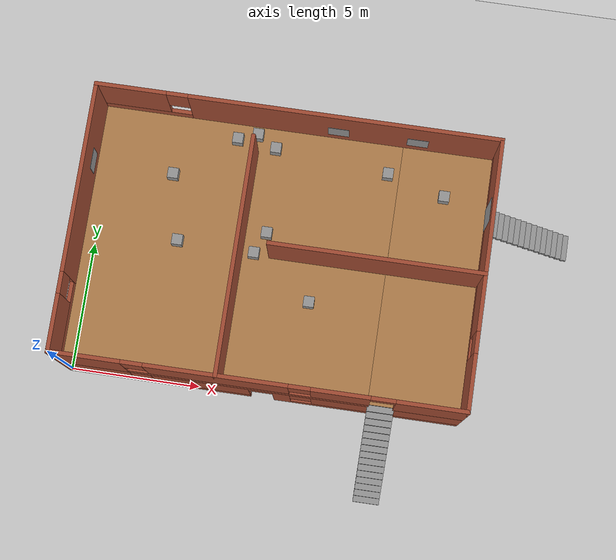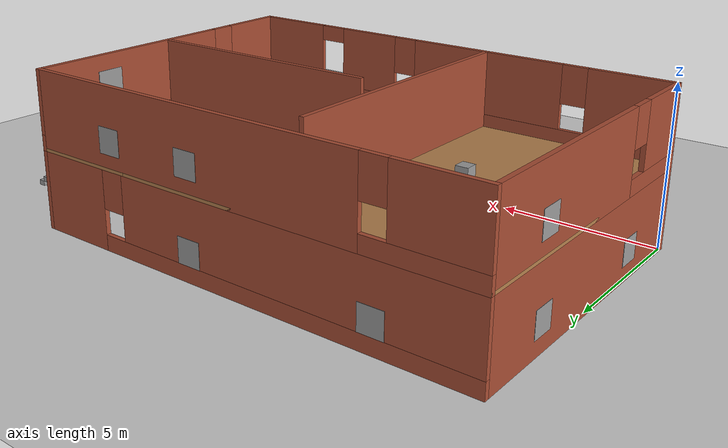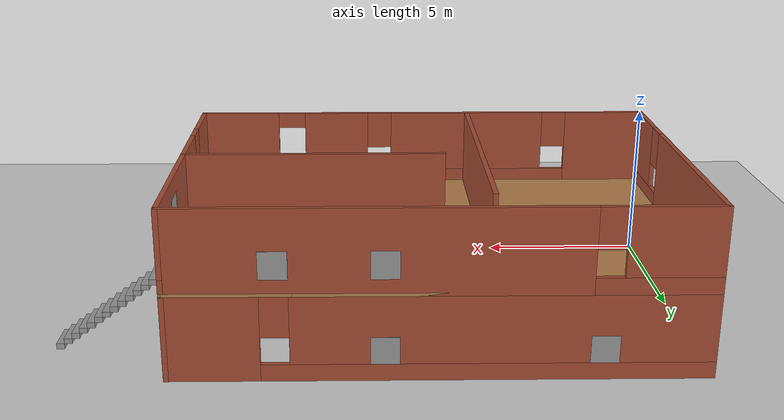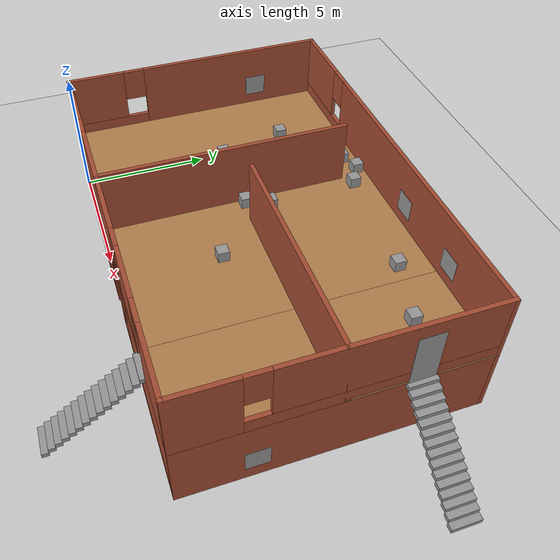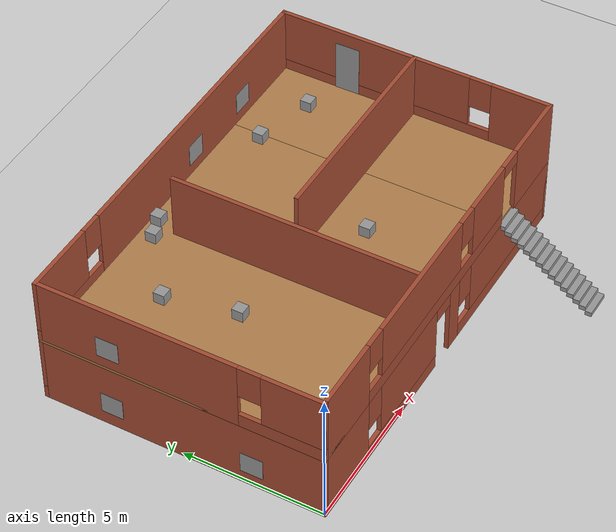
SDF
<sdf version='1.7'>
  <world name='default'>
    <light name='sun' type='directional'>
      <cast_shadows>1</cast_shadows>
      <pose>0 0 10 0 -0 0</pose>
      <diffuse>0.8 0.8 0.8 1</diffuse>
      <specular>0.2 0.2 0.2 1</specular>
      <attenuation>
        <range>1000</range>
        <constant>0.9</constant>
        <linear>0.01</linear>
        <quadratic>0.001</quadratic>
      </attenuation>
      <direction>-0.5 0.1 -0.9</direction>
      <spot>
        <inner_angle>0</inner_angle>
        <outer_angle>0</outer_angle>
        <falloff>0</falloff>
      </spot>
    </light>
    <model name='ground_plane'>
      <static>1</static>
      <link name='link'>
        <collision name='collision'>
          <geometry>
            <plane>
              <normal>0 0 1</normal>
              <size>100 100</size>
            </plane>
          </geometry>
          <surface>
            <friction>
              <ode>
                <mu>100</mu>
                <mu2>50</mu2>
              </ode>
              <torsional>
                <ode/>
              </torsional>
            </friction>
            <contact>
              <ode/>
            </contact>
            <bounce/>
          </surface>
          <max_contacts>10</max_contacts>
        </collision>
        <visual name='visual'>
          <cast_shadows>0</cast_shadows>
          <geometry>
            <plane>
              <normal>0 0 1</normal>
              <size>100 100</size>
            </plane>
          </geometry>
          <material>
            <script>
              <uri>file://media/materials/scripts/gazebo.material</uri>
              <name>Gazebo/Grey</name>
            </script>
          </material>
        </visual>
        <self_collide>0</self_collide>
        <enable_wind>0</enable_wind>
        <kinematic>0</kinematic>
      </link>
    </model>
    <gravity>0 0 -9.8</gravity>
    <magnetic_field>6e-06 2.3e-05 -4.2e-05</magnetic_field>
    <atmosphere type='adiabatic'/>
    <physics type='ode'>
      <max_step_size>0.001</max_step_size>
      <real_time_factor>1</real_time_factor>
      <real_time_update_rate>1000</real_time_update_rate>
    </physics>
    <scene>
      <ambient>0.4 0.4 0.4 1</ambient>
      <background>0.7 0.7 0.7 1</background>
      <shadows>1</shadows>
    </scene>
    <audio>
      <device>default</device>
    </audio>
    <wind/>
    <spherical_coordinates>
      <surface_model>EARTH_WGS84</surface_model>
      <latitude_deg>0</latitude_deg>
      <longitude_deg>0</longitude_deg>
      <elevation>0</elevation>
      <heading_deg>0</heading_deg>
    </spherical_coordinates>
    <model name='warehouse_automation'>
      <pose>9.2125 3.2875 0 0 -0 0</pose>
      <link name='Door_1'>
        <collision name='Door_1_Collision'>
          <geometry>
            <box>
              <size>0.9 0.17 2</size>
            </box>
          </geometry>
          <pose>0 0 1 0 -0 0</pose>
          <max_contacts>10</max_contacts>
          <surface>
            <contact>
              <ode/>
            </contact>
            <bounce/>
            <friction>
              <torsional>
                <ode/>
              </torsional>
              <ode/>
            </friction>
          </surface>
        </collision>
        <visual name='Door_1_Visual'>
          <pose>0 0 1 0 -0 0</pose>
          <geometry>
            <box>
              <size>0.9 0.17 2</size>
            </box>
          </geometry>
          <material>
            <script>
              <uri>file://media/materials/scripts/gazebo.material</uri>
              <name>Gazebo/Grey</name>
            </script>
          </material>
        </visual>
        <pose>5.7875 4.2125 2.5 0 -0 1.58891</pose>
        <self_collide>0</self_collide>
        <enable_wind>0</enable_wind>
        <kinematic>0</kinematic>
      </link>
      <link name='Floor_0'>
        <pose>-1.7125 1.7125 2.5 0 -0 0</pose>
        <visual name='Floor_0_Visual_0'>
          <pose>-1.7875 0 0.05 0 -0 0</pose>
          <geometry>
            <box>
              <size>11.575 10.15 0.1</size>
            </box>
          </geometry>
          <material>
            <script>
              <uri>file://media/materials/scripts/gazebo.material</uri>
              <name>Gazebo/Wood</name>
            </script>
            <ambient>0.835294 0.780392 0.478431 1</ambient>
          </material>
          <meta>
            <layer>1</layer>
          </meta>
        </visual>
        <collision name='Floor_0_Collision_0'>
          <geometry>
            <box>
              <size>11.575 10.15 0.1</size>
            </box>
          </geometry>
          <pose>-1.7875 0 0.05 0 -0 0</pose>
          <max_contacts>10</max_contacts>
          <surface>
            <contact>
              <ode/>
            </contact>
            <bounce/>
            <friction>
              <torsional>
                <ode/>
              </torsional>
              <ode/>
            </friction>
          </surface>
        </collision>
        <visual name='Floor_0_Visual_1'>
          <pose>5.75 0.0375 0.05 0 -0 0</pose>
          <geometry>
            <box>
              <size>3.5 10.075 0.1</size>
            </box>
          </geometry>
          <material>
            <script>
              <uri>file://media/materials/scripts/gazebo.material</uri>
              <name>Gazebo/Wood</name>
            </script>
            <ambient>0.835294 0.780392 0.478431 1</ambient>
          </material>
          <meta>
            <layer>1</layer>
          </meta>
        </visual>
        <collision name='Floor_0_Collision_1'>
          <geometry>
            <box>
              <size>3.5 10.075 0.1</size>
            </box>
          </geometry>
          <pose>5.75 0.0375 0.05 0 -0 0</pose>
          <max_contacts>10</max_contacts>
          <surface>
            <contact>
              <ode/>
            </contact>
            <bounce/>
            <friction>
              <torsional>
                <ode/>
              </torsional>
              <ode/>
            </friction>
          </surface>
        </collision>
        <visual name='Floor_0_Visual_2'>
          <pose>7.5375 -1.5 0.05 0 -0 0</pose>
          <geometry>
            <box>
              <size>0.075 7 0.1</size>
            </box>
          </geometry>
          <material>
            <script>
              <uri>file://media/materials/scripts/gazebo.material</uri>
              <name>Gazebo/Wood</name>
            </script>
            <ambient>0.835294 0.780392 0.478431 1</ambient>
          </material>
          <meta>
            <layer>1</layer>
          </meta>
        </visual>
        <collision name='Floor_0_Collision_2'>
          <geometry>
            <box>
              <size>0.075 7 0.1</size>
            </box>
          </geometry>
          <pose>7.5375 -1.5 0.05 0 -0 0</pose>
          <max_contacts>10</max_contacts>
          <surface>
            <contact>
              <ode/>
            </contact>
            <bounce/>
            <friction>
              <torsional>
                <ode/>
              </torsional>
              <ode/>
            </friction>
          </surface>
        </collision>
        <visual name='Floor_0_Visual_3'>
          <pose>7.5375 4.0375 0.05 0 -0 0</pose>
          <geometry>
            <box>
              <size>0.075 2.075 0.1</size>
            </box>
          </geometry>
          <material>
            <script>
              <uri>file://media/materials/scripts/gazebo.material</uri>
              <name>Gazebo/Wood</name>
            </script>
            <ambient>0.835294 0.780392 0.478431 1</ambient>
          </material>
          <meta>
            <layer>1</layer>
          </meta>
        </visual>
        <collision name='Floor_0_Collision_3'>
          <geometry>
            <box>
              <size>0.075 2.075 0.1</size>
            </box>
          </geometry>
          <pose>7.5375 4.0375 0.05 0 -0 0</pose>
          <max_contacts>10</max_contacts>
          <surface>
            <contact>
              <ode/>
            </contact>
            <bounce/>
            <friction>
              <torsional>
                <ode/>
              </torsional>
              <ode/>
            </friction>
          </surface>
        </collision>
        <self_collide>0</self_collide>
        <enable_wind>0</enable_wind>
        <kinematic>0</kinematic>
      </link>
      <link name='Stairs_0'>
        <visual name='Stairs_0_Visual_0'>
          <pose>2.7875 -6.67083 0.083333 0 -0 -3.14159</pose>
          <geometry>
            <box>
              <size>1 0.233333 0.166667</size>
            </box>
          </geometry>
          <material>
            <script>
              <uri>file://media/materials/scripts/gazebo.material</uri>
              <name>Gazebo/Grey</name>
            </script>
            <ambient>0.435294 0.454902 0.47451 1</ambient>
          </material>
          <meta>
            <layer>0</layer>
          </meta>
        </visual>
        <collision name='Stairs_0_Collision_0'>
          <geometry>
            <box>
              <size>1 0.233333 0.166667</size>
            </box>
          </geometry>
          <pose>2.7875 -6.67083 0.083333 0 -0 -3.14159</pose>
          <max_contacts>10</max_contacts>
          <surface>
            <contact>
              <ode/>
            </contact>
            <bounce/>
            <friction>
              <torsional>
                <ode/>
              </torsional>
              <ode/>
            </friction>
          </surface>
        </collision>
        <visual name='Stairs_0_Visual_1'>
          <pose>2.7875 -6.4375 0.25 0 -0 -3.14159</pose>
          <geometry>
            <box>
              <size>1 0.233333 0.166667</size>
            </box>
          </geometry>
          <material>
            <script>
              <uri>file://media/materials/scripts/gazebo.material</uri>
              <name>Gazebo/Grey</name>
            </script>
            <ambient>0.435294 0.454902 0.47451 1</ambient>
          </material>
          <meta>
            <layer>0</layer>
          </meta>
        </visual>
        <collision name='Stairs_0_Collision_1'>
          <geometry>
            <box>
              <size>1 0.233333 0.166667</size>
            </box>
          </geometry>
          <pose>2.7875 -6.4375 0.25 0 -0 -3.14159</pose>
          <max_contacts>10</max_contacts>
          <surface>
            <contact>
              <ode/>
            </contact>
            <bounce/>
            <friction>
              <torsional>
                <ode/>
              </torsional>
              <ode/>
            </friction>
          </surface>
        </collision>
        <visual name='Stairs_0_Visual_2'>
          <pose>2.7875 -6.20417 0.416667 0 -0 -3.14159</pose>
          <geometry>
            <box>
              <size>1 0.233333 0.166667</size>
            </box>
          </geometry>
          <material>
            <script>
              <uri>file://media/materials/scripts/gazebo.material</uri>
              <name>Gazebo/Grey</name>
            </script>
            <ambient>0.435294 0.454902 0.47451 1</ambient>
          </material>
          <meta>
            <layer>0</layer>
          </meta>
        </visual>
        <collision name='Stairs_0_Collision_2'>
          <geometry>
            <box>
              <size>1 0.233333 0.166667</size>
            </box>
          </geometry>
          <pose>2.7875 -6.20417 0.416667 0 -0 -3.14159</pose>
          <max_contacts>10</max_contacts>
          <surface>
            <contact>
              <ode/>
            </contact>
            <bounce/>
            <friction>
              <torsional>
                <ode/>
              </torsional>
              <ode/>
            </friction>
          </surface>
        </collision>
        <visual name='Stairs_0_Visual_3'>
          <pose>2.7875 -5.97083 0.583333 0 -0 -3.14159</pose>
          <geometry>
            <box>
              <size>1 0.233333 0.166667</size>
            </box>
          </geometry>
          <material>
            <script>
              <uri>file://media/materials/scripts/gazebo.material</uri>
              <name>Gazebo/Grey</name>
            </script>
            <ambient>0.435294 0.454902 0.47451 1</ambient>
          </material>
          <meta>
            <layer>0</layer>
          </meta>
        </visual>
        <collision name='Stairs_0_Collision_3'>
          <geometry>
            <box>
              <size>1 0.233333 0.166667</size>
            </box>
          </geometry>
          <pose>2.7875 -5.97083 0.583333 0 -0 -3.14159</pose>
          <max_contacts>10</max_contacts>
          <surface>
            <contact>
              <ode/>
            </contact>
            <bounce/>
            <friction>
              <torsional>
                <ode/>
              </torsional>
              <ode/>
            </friction>
          </surface>
        </collision>
        <visual name='Stairs_0_Visual_4'>
          <pose>2.7875 -5.7375 0.75 0 -0 -3.14159</pose>
          <geometry>
            <box>
              <size>1 0.233333 0.166667</size>
            </box>
          </geometry>
          <material>
            <script>
              <uri>file://media/materials/scripts/gazebo.material</uri>
              <name>Gazebo/Grey</name>
            </script>
            <ambient>0.435294 0.454902 0.47451 1</ambient>
          </material>
          <meta>
            <layer>0</layer>
          </meta>
        </visual>
        <collision name='Stairs_0_Collision_4'>
          <geometry>
            <box>
              <size>1 0.233333 0.166667</size>
            </box>
          </geometry>
          <pose>2.7875 -5.7375 0.75 0 -0 -3.14159</pose>
          <max_contacts>10</max_contacts>
          <surface>
            <contact>
              <ode/>
            </contact>
            <bounce/>
            <friction>
              <torsional>
                <ode/>
              </torsional>
              <ode/>
            </friction>
          </surface>
        </collision>
        <visual name='Stairs_0_Visual_5'>
          <pose>2.7875 -5.50417 0.916667 0 -0 -3.14159</pose>
          <geometry>
            <box>
              <size>1 0.233333 0.166667</size>
            </box>
          </geometry>
          <material>
            <script>
              <uri>file://media/materials/scripts/gazebo.material</uri>
              <name>Gazebo/Grey</name>
            </script>
            <ambient>0.435294 0.454902 0.47451 1</ambient>
          </material>
          <meta>
            <layer>0</layer>
          </meta>
        </visual>
        <collision name='Stairs_0_Collision_5'>
          <geometry>
            <box>
              <size>1 0.233333 0.166667</size>
            </box>
          </geometry>
          <pose>2.7875 -5.50417 0.916667 0 -0 -3.14159</pose>
          <max_contacts>10</max_contacts>
          <surface>
            <contact>
              <ode/>
            </contact>
            <bounce/>
            <friction>
              <torsional>
                <ode/>
              </torsional>
              <ode/>
            </friction>
          </surface>
        </collision>
        <visual name='Stairs_0_Visual_6'>
          <pose>2.7875 -5.27083 1.08333 0 -0 -3.14159</pose>
          <geometry>
            <box>
              <size>1 0.233333 0.166667</size>
            </box>
          </geometry>
          <material>
            <script>
              <uri>file://media/materials/scripts/gazebo.material</uri>
              <name>Gazebo/Grey</name>
            </script>
            <ambient>0.435294 0.454902 0.47451 1</ambient>
          </material>
          <meta>
            <layer>0</layer>
          </meta>
        </visual>
        <collision name='Stairs_0_Collision_6'>
          <geometry>
            <box>
              <size>1 0.233333 0.166667</size>
            </box>
          </geometry>
          <pose>2.7875 -5.27083 1.08333 0 -0 -3.14159</pose>
          <max_contacts>10</max_contacts>
          <surface>
            <contact>
              <ode/>
            </contact>
            <bounce/>
            <friction>
              <torsional>
                <ode/>
              </torsional>
              <ode/>
            </friction>
          </surface>
        </collision>
        <visual name='Stairs_0_Visual_7'>
          <pose>2.7875 -5.0375 1.25 0 -0 -3.14159</pose>
          <geometry>
            <box>
              <size>1 0.233333 0.166667</size>
            </box>
          </geometry>
          <material>
            <script>
              <uri>file://media/materials/scripts/gazebo.material</uri>
              <name>Gazebo/Grey</name>
            </script>
            <ambient>0.435294 0.454902 0.47451 1</ambient>
          </material>
          <meta>
            <layer>0</layer>
          </meta>
        </visual>
        <collision name='Stairs_0_Collision_7'>
          <geometry>
            <box>
              <size>1 0.233333 0.166667</size>
            </box>
          </geometry>
          <pose>2.7875 -5.0375 1.25 0 -0 -3.14159</pose>
          <max_contacts>10</max_contacts>
          <surface>
            <contact>
              <ode/>
            </contact>
            <bounce/>
            <friction>
              <torsional>
                <ode/>
              </torsional>
              <ode/>
            </friction>
          </surface>
        </collision>
        <visual name='Stairs_0_Visual_8'>
          <pose>2.7875 -4.80417 1.41667 0 -0 -3.14159</pose>
          <geometry>
            <box>
              <size>1 0.233333 0.166667</size>
            </box>
          </geometry>
          <material>
            <script>
              <uri>file://media/materials/scripts/gazebo.material</uri>
              <name>Gazebo/Grey</name>
            </script>
            <ambient>0.435294 0.454902 0.47451 1</ambient>
          </material>
          <meta>
            <layer>0</layer>
          </meta>
        </visual>
        <collision name='Stairs_0_Collision_8'>
          <geometry>
            <box>
              <size>1 0.233333 0.166667</size>
            </box>
          </geometry>
          <pose>2.7875 -4.80417 1.41667 0 -0 -3.14159</pose>
          <max_contacts>10</max_contacts>
          <surface>
            <contact>
              <ode/>
            </contact>
            <bounce/>
            <friction>
              <torsional>
                <ode/>
              </torsional>
              <ode/>
            </friction>
          </surface>
        </collision>
        <visual name='Stairs_0_Visual_9'>
          <pose>2.7875 -4.57083 1.58333 0 -0 -3.14159</pose>
          <geometry>
            <box>
              <size>1 0.233333 0.166667</size>
            </box>
          </geometry>
          <material>
            <script>
              <uri>file://media/materials/scripts/gazebo.material</uri>
              <name>Gazebo/Grey</name>
            </script>
            <ambient>0.435294 0.454902 0.47451 1</ambient>
          </material>
          <meta>
            <layer>0</layer>
          </meta>
        </visual>
        <collision name='Stairs_0_Collision_9'>
          <geometry>
            <box>
              <size>1 0.233333 0.166667</size>
            </box>
          </geometry>
          <pose>2.7875 -4.57083 1.58333 0 -0 -3.14159</pose>
          <max_contacts>10</max_contacts>
          <surface>
            <contact>
              <ode/>
            </contact>
            <bounce/>
            <friction>
              <torsional>
                <ode/>
              </torsional>
              <ode/>
            </friction>
          </surface>
        </collision>
        <visual name='Stairs_0_Visual_10'>
          <pose>2.7875 -4.3375 1.75 0 -0 -3.14159</pose>
          <geometry>
            <box>
              <size>1 0.233333 0.166667</size>
            </box>
          </geometry>
          <material>
            <script>
              <uri>file://media/materials/scripts/gazebo.material</uri>
              <name>Gazebo/Grey</name>
            </script>
            <ambient>0.435294 0.454902 0.47451 1</ambient>
          </material>
          <meta>
            <layer>0</layer>
          </meta>
        </visual>
        <collision name='Stairs_0_Collision_10'>
          <geometry>
            <box>
              <size>1 0.233333 0.166667</size>
            </box>
          </geometry>
          <pose>2.7875 -4.3375 1.75 0 -0 -3.14159</pose>
          <max_contacts>10</max_contacts>
          <surface>
            <contact>
              <ode/>
            </contact>
            <bounce/>
            <friction>
              <torsional>
                <ode/>
              </torsional>
              <ode/>
            </friction>
          </surface>
        </collision>
        <visual name='Stairs_0_Visual_11'>
          <pose>2.7875 -4.10417 1.91667 0 -0 -3.14159</pose>
          <geometry>
            <box>
              <size>1 0.233333 0.166667</size>
            </box>
          </geometry>
          <material>
            <script>
              <uri>file://media/materials/scripts/gazebo.material</uri>
              <name>Gazebo/Grey</name>
            </script>
            <ambient>0.435294 0.454902 0.47451 1</ambient>
          </material>
          <meta>
            <layer>0</layer>
          </meta>
        </visual>
        <collision name='Stairs_0_Collision_11'>
          <geometry>
            <box>
              <size>1 0.233333 0.166667</size>
            </box>
          </geometry>
          <pose>2.7875 -4.10417 1.91667 0 -0 -3.14159</pose>
          <max_contacts>10</max_contacts>
          <surface>
            <contact>
              <ode/>
            </contact>
            <bounce/>
            <friction>
              <torsional>
                <ode/>
              </torsional>
              <ode/>
            </friction>
          </surface>
        </collision>
        <visual name='Stairs_0_Visual_12'>
          <pose>2.7875 -3.87083 2.08333 0 -0 -3.14159</pose>
          <geometry>
            <box>
              <size>1 0.233333 0.166667</size>
            </box>
          </geometry>
          <material>
            <script>
              <uri>file://media/materials/scripts/gazebo.material</uri>
              <name>Gazebo/Grey</name>
            </script>
            <ambient>0.435294 0.454902 0.47451 1</ambient>
          </material>
          <meta>
            <layer>0</layer>
          </meta>
        </visual>
        <collision name='Stairs_0_Collision_12'>
          <geometry>
            <box>
              <size>1 0.233333 0.166667</size>
            </box>
          </geometry>
          <pose>2.7875 -3.87083 2.08333 0 -0 -3.14159</pose>
          <max_contacts>10</max_contacts>
          <surface>
            <contact>
              <ode/>
            </contact>
            <bounce/>
            <friction>
              <torsional>
                <ode/>
              </torsional>
              <ode/>
            </friction>
          </surface>
        </collision>
        <visual name='Stairs_0_Visual_13'>
          <pose>2.7875 -3.6375 2.25 0 -0 -3.14159</pose>
          <geometry>
            <box>
              <size>1 0.233333 0.166667</size>
            </box>
          </geometry>
          <material>
            <script>
              <uri>file://media/materials/scripts/gazebo.material</uri>
              <name>Gazebo/Grey</name>
            </script>
            <ambient>0.435294 0.454902 0.47451 1</ambient>
          </material>
          <meta>
            <layer>0</layer>
          </meta>
        </visual>
        <collision name='Stairs_0_Collision_13'>
          <geometry>
            <box>
              <size>1 0.233333 0.166667</size>
            </box>
          </geometry>
          <pose>2.7875 -3.6375 2.25 0 -0 -3.14159</pose>
          <max_contacts>10</max_contacts>
          <surface>
            <contact>
              <ode/>
            </contact>
            <bounce/>
            <friction>
              <torsional>
                <ode/>
              </torsional>
              <ode/>
            </friction>
          </surface>
        </collision>
        <visual name='Stairs_0_Visual_14'>
          <pose>2.7875 -3.40417 2.41667 0 -0 -3.14159</pose>
          <geometry>
            <box>
              <size>1 0.233333 0.166667</size>
            </box>
          </geometry>
          <material>
            <script>
              <uri>file://media/materials/scripts/gazebo.material</uri>
              <name>Gazebo/Grey</name>
            </script>
            <ambient>0.435294 0.454902 0.47451 1</ambient>
          </material>
          <meta>
            <layer>0</layer>
          </meta>
        </visual>
        <collision name='Stairs_0_Collision_14'>
          <geometry>
            <box>
              <size>1 0.233333 0.166667</size>
            </box>
          </geometry>
          <pose>2.7875 -3.40417 2.41667 0 -0 -3.14159</pose>
          <max_contacts>10</max_contacts>
          <surface>
            <contact>
              <ode/>
            </contact>
            <bounce/>
            <friction>
              <torsional>
                <ode/>
              </torsional>
              <ode/>
            </friction>
          </surface>
        </collision>
        <self_collide>0</self_collide>
        <enable_wind>0</enable_wind>
        <kinematic>0</kinematic>
      </link>
      <link name='Stairs_1'>
        <visual name='Stairs_1_Visual_0'>
          <pose>9.17083 4.2125 0.083333 0 -0 -1.5708</pose>
          <geometry>
            <box>
              <size>1 0.233333 0.166667</size>
            </box>
          </geometry>
          <material>
            <script>
              <uri>file://media/materials/scripts/gazebo.material</uri>
              <name>Gazebo/Grey</name>
            </script>
            <ambient>1 1 1 1</ambient>
          </material>
          <meta>
            <layer>0</layer>
          </meta>
        </visual>
        <collision name='Stairs_1_Collision_0'>
          <geometry>
            <box>
              <size>1 0.233333 0.166667</size>
            </box>
          </geometry>
          <pose>9.17083 4.2125 0.083333 0 -0 -1.5708</pose>
          <max_contacts>10</max_contacts>
          <surface>
            <contact>
              <ode/>
            </contact>
            <bounce/>
            <friction>
              <torsional>
                <ode/>
              </torsional>
              <ode/>
            </friction>
          </surface>
        </collision>
        <visual name='Stairs_1_Visual_1'>
          <pose>8.9375 4.2125 0.25 0 -0 -1.5708</pose>
          <geometry>
            <box>
              <size>1 0.233333 0.166667</size>
            </box>
          </geometry>
          <material>
            <script>
              <uri>file://media/materials/scripts/gazebo.material</uri>
              <name>Gazebo/Grey</name>
            </script>
            <ambient>1 1 1 1</ambient>
          </material>
          <meta>
            <layer>0</layer>
          </meta>
        </visual>
        <collision name='Stairs_1_Collision_1'>
          <geometry>
            <box>
              <size>1 0.233333 0.166667</size>
            </box>
          </geometry>
          <pose>8.9375 4.2125 0.25 0 -0 -1.5708</pose>
          <max_contacts>10</max_contacts>
          <surface>
            <contact>
              <ode/>
            </contact>
            <bounce/>
            <friction>
              <torsional>
                <ode/>
              </torsional>
              <ode/>
            </friction>
          </surface>
        </collision>
        <visual name='Stairs_1_Visual_2'>
          <pose>8.70417 4.2125 0.416667 0 -0 -1.5708</pose>
          <geometry>
            <box>
              <size>1 0.233333 0.166667</size>
            </box>
          </geometry>
          <material>
            <script>
              <uri>file://media/materials/scripts/gazebo.material</uri>
              <name>Gazebo/Grey</name>
            </script>
            <ambient>1 1 1 1</ambient>
          </material>
          <meta>
            <layer>0</layer>
          </meta>
        </visual>
        <collision name='Stairs_1_Collision_2'>
          <geometry>
            <box>
              <size>1 0.233333 0.166667</size>
            </box>
          </geometry>
          <pose>8.70417 4.2125 0.416667 0 -0 -1.5708</pose>
          <max_contacts>10</max_contacts>
          <surface>
            <contact>
              <ode/>
            </contact>
            <bounce/>
            <friction>
              <torsional>
                <ode/>
              </torsional>
              <ode/>
            </friction>
          </surface>
        </collision>
        <visual name='Stairs_1_Visual_3'>
          <pose>8.47083 4.2125 0.583333 0 -0 -1.5708</pose>
          <geometry>
            <box>
              <size>1 0.233333 0.166667</size>
            </box>
          </geometry>
          <material>
            <script>
              <uri>file://media/materials/scripts/gazebo.material</uri>
              <name>Gazebo/Grey</name>
            </script>
            <ambient>1 1 1 1</ambient>
          </material>
          <meta>
            <layer>0</layer>
          </meta>
        </visual>
        <collision name='Stairs_1_Collision_3'>
          <geometry>
            <box>
              <size>1 0.233333 0.166667</size>
            </box>
          </geometry>
          <pose>8.47083 4.2125 0.583333 0 -0 -1.5708</pose>
          <max_contacts>10</max_contacts>
          <surface>
            <contact>
              <ode/>
            </contact>
            <bounce/>
            <friction>
              <torsional>
                <ode/>
              </torsional>
              <ode/>
            </friction>
          </surface>
        </collision>
        <visual name='Stairs_1_Visual_4'>
          <pose>8.2375 4.2125 0.75 0 -0 -1.5708</pose>
          <geometry>
            <box>
              <size>1 0.233333 0.166667</size>
            </box>
          </geometry>
          <material>
            <script>
              <uri>file://media/materials/scripts/gazebo.material</uri>
              <name>Gazebo/Grey</name>
            </script>
            <ambient>1 1 1 1</ambient>
          </material>
          <meta>
            <layer>0</layer>
          </meta>
        </visual>
        <collision name='Stairs_1_Collision_4'>
          <geometry>
            <box>
              <size>1 0.233333 0.166667</size>
            </box>
          </geometry>
          <pose>8.2375 4.2125 0.75 0 -0 -1.5708</pose>
          <max_contacts>10</max_contacts>
          <surface>
            <contact>
              <ode/>
            </contact>
            <bounce/>
            <friction>
              <torsional>
                <ode/>
              </torsional>
              <ode/>
            </friction>
          </surface>
        </collision>
        <visual name='Stairs_1_Visual_5'>
          <pose>8.00417 4.2125 0.916667 0 -0 -1.5708</pose>
          <geometry>
            <box>
              <size>1 0.233333 0.166667</size>
            </box>
          </geometry>
          <material>
            <script>
              <uri>file://media/materials/scripts/gazebo.material</uri>
              <name>Gazebo/Grey</name>
            </script>
            <ambient>1 1 1 1</ambient>
          </material>
          <meta>
            <layer>0</layer>
          </meta>
        </visual>
        <collision name='Stairs_1_Collision_5'>
          <geometry>
            <box>
              <size>1 0.233333 0.166667</size>
            </box>
          </geometry>
          <pose>8.00417 4.2125 0.916667 0 -0 -1.5708</pose>
          <max_contacts>10</max_contacts>
          <surface>
            <contact>
              <ode/>
            </contact>
            <bounce/>
            <friction>
              <torsional>
                <ode/>
              </torsional>
              <ode/>
            </friction>
          </surface>
        </collision>
        <visual name='Stairs_1_Visual_6'>
          <pose>7.77083 4.2125 1.08333 0 -0 -1.5708</pose>
          <geometry>
            <box>
              <size>1 0.233333 0.166667</size>
            </box>
          </geometry>
          <material>
            <script>
              <uri>file://media/materials/scripts/gazebo.material</uri>
              <name>Gazebo/Grey</name>
            </script>
            <ambient>1 1 1 1</ambient>
          </material>
          <meta>
            <layer>0</layer>
          </meta>
        </visual>
        <collision name='Stairs_1_Collision_6'>
          <geometry>
            <box>
              <size>1 0.233333 0.166667</size>
            </box>
          </geometry>
          <pose>7.77083 4.2125 1.08333 0 -0 -1.5708</pose>
          <max_contacts>10</max_contacts>
          <surface>
            <contact>
              <ode/>
            </contact>
            <bounce/>
            <friction>
              <torsional>
                <ode/>
              </torsional>
              <ode/>
            </friction>
          </surface>
        </collision>
        <visual name='Stairs_1_Visual_7'>
          <pose>7.5375 4.2125 1.25 0 -0 -1.5708</pose>
          <geometry>
            <box>
              <size>1 0.233333 0.166667</size>
            </box>
          </geometry>
          <material>
            <script>
              <uri>file://media/materials/scripts/gazebo.material</uri>
              <name>Gazebo/Grey</name>
            </script>
            <ambient>1 1 1 1</ambient>
          </material>
          <meta>
            <layer>0</layer>
          </meta>
        </visual>
        <collision name='Stairs_1_Collision_7'>
          <geometry>
            <box>
              <size>1 0.233333 0.166667</size>
            </box>
          </geometry>
          <pose>7.5375 4.2125 1.25 0 -0 -1.5708</pose>
          <max_contacts>10</max_contacts>
          <surface>
            <contact>
              <ode/>
            </contact>
            <bounce/>
            <friction>
              <torsional>
                <ode/>
              </torsional>
              <ode/>
            </friction>
          </surface>
        </collision>
        <visual name='Stairs_1_Visual_8'>
          <pose>7.30417 4.2125 1.41667 0 -0 -1.5708</pose>
          <geometry>
            <box>
              <size>1 0.233333 0.166667</size>
            </box>
          </geometry>
          <material>
            <script>
              <uri>file://media/materials/scripts/gazebo.material</uri>
              <name>Gazebo/Grey</name>
            </script>
            <ambient>1 1 1 1</ambient>
          </material>
          <meta>
            <layer>0</layer>
          </meta>
        </visual>
        <collision name='Stairs_1_Collision_8'>
          <geometry>
            <box>
              <size>1 0.233333 0.166667</size>
            </box>
          </geometry>
          <pose>7.30417 4.2125 1.41667 0 -0 -1.5708</pose>
          <max_contacts>10</max_contacts>
          <surface>
            <contact>
              <ode/>
            </contact>
            <bounce/>
            <friction>
              <torsional>
                <ode/>
              </torsional>
              <ode/>
            </friction>
          </surface>
        </collision>
        <visual name='Stairs_1_Visual_9'>
          <pose>7.07083 4.2125 1.58333 0 -0 -1.5708</pose>
          <geometry>
            <box>
              <size>1 0.233333 0.166667</size>
            </box>
          </geometry>
          <material>
            <script>
              <uri>file://media/materials/scripts/gazebo.material</uri>
              <name>Gazebo/Grey</name>
            </script>
            <ambient>1 1 1 1</ambient>
          </material>
          <meta>
            <layer>0</layer>
          </meta>
        </visual>
        <collision name='Stairs_1_Collision_9'>
          <geometry>
            <box>
              <size>1 0.233333 0.166667</size>
            </box>
          </geometry>
          <pose>7.07083 4.2125 1.58333 0 -0 -1.5708</pose>
          <max_contacts>10</max_contacts>
          <surface>
            <contact>
              <ode/>
            </contact>
            <bounce/>
            <friction>
              <torsional>
                <ode/>
              </torsional>
              <ode/>
            </friction>
          </surface>
        </collision>
        <visual name='Stairs_1_Visual_10'>
          <pose>6.8375 4.2125 1.75 0 -0 -1.5708</pose>
          <geometry>
            <box>
              <size>1 0.233333 0.166667</size>
            </box>
          </geometry>
          <material>
            <script>
              <uri>file://media/materials/scripts/gazebo.material</uri>
              <name>Gazebo/Grey</name>
            </script>
            <ambient>1 1 1 1</ambient>
          </material>
          <meta>
            <layer>0</layer>
          </meta>
        </visual>
        <collision name='Stairs_1_Collision_10'>
          <geometry>
            <box>
              <size>1 0.233333 0.166667</size>
            </box>
          </geometry>
          <pose>6.8375 4.2125 1.75 0 -0 -1.5708</pose>
          <max_contacts>10</max_contacts>
          <surface>
            <contact>
              <ode/>
            </contact>
            <bounce/>
            <friction>
              <torsional>
                <ode/>
              </torsional>
              <ode/>
            </friction>
          </surface>
        </collision>
        <visual name='Stairs_1_Visual_11'>
          <pose>6.60417 4.2125 1.91667 0 -0 -1.5708</pose>
          <geometry>
            <box>
              <size>1 0.233333 0.166667</size>
            </box>
          </geometry>
          <material>
            <script>
              <uri>file://media/materials/scripts/gazebo.material</uri>
              <name>Gazebo/Grey</name>
            </script>
            <ambient>1 1 1 1</ambient>
          </material>
          <meta>
            <layer>0</layer>
          </meta>
        </visual>
        <collision name='Stairs_1_Collision_11'>
          <geometry>
            <box>
              <size>1 0.233333 0.166667</size>
            </box>
          </geometry>
          <pose>6.60417 4.2125 1.91667 0 -0 -1.5708</pose>
          <max_contacts>10</max_contacts>
          <surface>
            <contact>
              <ode/>
            </contact>
            <bounce/>
            <friction>
              <torsional>
                <ode/>
              </torsional>
              <ode/>
            </friction>
          </surface>
        </collision>
        <visual name='Stairs_1_Visual_12'>
          <pose>6.37083 4.2125 2.08333 0 -0 -1.5708</pose>
          <geometry>
            <box>
              <size>1 0.233333 0.166667</size>
            </box>
          </geometry>
          <material>
            <script>
              <uri>file://media/materials/scripts/gazebo.material</uri>
              <name>Gazebo/Grey</name>
            </script>
            <ambient>1 1 1 1</ambient>
          </material>
          <meta>
            <layer>0</layer>
          </meta>
        </visual>
        <collision name='Stairs_1_Collision_12'>
          <geometry>
            <box>
              <size>1 0.233333 0.166667</size>
            </box>
          </geometry>
          <pose>6.37083 4.2125 2.08333 0 -0 -1.5708</pose>
          <max_contacts>10</max_contacts>
          <surface>
            <contact>
              <ode/>
            </contact>
            <bounce/>
            <friction>
              <torsional>
                <ode/>
              </torsional>
              <ode/>
            </friction>
          </surface>
        </collision>
        <visual name='Stairs_1_Visual_13'>
          <pose>6.1375 4.2125 2.25 0 -0 -1.5708</pose>
          <geometry>
            <box>
              <size>1 0.233333 0.166667</size>
            </box>
          </geometry>
          <material>
            <script>
              <uri>file://media/materials/scripts/gazebo.material</uri>
              <name>Gazebo/Grey</name>
            </script>
            <ambient>1 1 1 1</ambient>
          </material>
          <meta>
            <layer>0</layer>
          </meta>
        </visual>
        <collision name='Stairs_1_Collision_13'>
          <geometry>
            <box>
              <size>1 0.233333 0.166667</size>
            </box>
          </geometry>
          <pose>6.1375 4.2125 2.25 0 -0 -1.5708</pose>
          <max_contacts>10</max_contacts>
          <surface>
            <contact>
              <ode/>
            </contact>
            <bounce/>
            <friction>
              <torsional>
                <ode/>
              </torsional>
              <ode/>
            </friction>
          </surface>
        </collision>
        <visual name='Stairs_1_Visual_14'>
          <pose>5.90417 4.2125 2.41667 0 -0 -1.5708</pose>
          <geometry>
            <box>
              <size>1 0.233333 0.166667</size>
            </box>
          </geometry>
          <material>
            <script>
              <uri>file://media/materials/scripts/gazebo.material</uri>
              <name>Gazebo/Grey</name>
            </script>
            <ambient>1 1 1 1</ambient>
          </material>
          <meta>
            <layer>0</layer>
          </meta>
        </visual>
        <collision name='Stairs_1_Collision_14'>
          <geometry>
            <box>
              <size>1 0.233333 0.166667</size>
            </box>
          </geometry>
          <pose>5.90417 4.2125 2.41667 0 -0 -1.5708</pose>
          <max_contacts>10</max_contacts>
          <surface>
            <contact>
              <ode/>
            </contact>
            <bounce/>
            <friction>
              <torsional>
                <ode/>
              </torsional>
              <ode/>
            </friction>
          </surface>
        </collision>
        <self_collide>0</self_collide>
        <enable_wind>0</enable_wind>
        <kinematic>0</kinematic>
      </link>
      <link name='Wall_0'>
        <pose>-1.7125 -3.2875 0 0 -0 0</pose>
        <visual name='Wall_0_Visual_0'>
          <pose>-6.2375 0 1.25 0 -0 0</pose>
          <geometry>
            <box>
              <size>2.675 0.15 2.5</size>
            </box>
          </geometry>
          <material>
            <script>
              <uri>file://media/materials/scripts/gazebo.material</uri>
              <name>Gazebo/Bricks</name>
            </script>
            <ambient>1 1 1 1</ambient>
          </material>
          <meta>
            <layer>0</layer>
          </meta>
        </visual>
        <collision name='Wall_0_Collision_0'>
          <geometry>
            <box>
              <size>2.675 0.15 2.5</size>
            </box>
          </geometry>
          <pose>-6.2375 0 1.25 0 -0 0</pose>
          <max_contacts>10</max_contacts>
          <surface>
            <contact>
              <ode/>
            </contact>
            <bounce/>
            <friction>
              <torsional>
                <ode/>
              </torsional>
              <ode/>
            </friction>
          </surface>
        </collision>
        <visual name='Wall_0_Visual_1'>
          <pose>0.775 0 1.25 0 -0 0</pose>
          <geometry>
            <box>
              <size>0.65 0.15 2.5</size>
            </box>
          </geometry>
          <material>
            <script>
              <uri>file://media/materials/scripts/gazebo.material</uri>
              <name>Gazebo/Bricks</name>
            </script>
            <ambient>1 1 1 1</ambient>
          </material>
          <meta>
            <layer>0</layer>
          </meta>
        </visual>
        <collision name='Wall_0_Collision_1'>
          <geometry>
            <box>
              <size>0.65 0.15 2.5</size>
            </box>
          </geometry>
          <pose>0.775 0 1.25 0 -0 0</pose>
          <max_contacts>10</max_contacts>
          <surface>
            <contact>
              <ode/>
            </contact>
            <bounce/>
            <friction>
              <torsional>
                <ode/>
              </torsional>
              <ode/>
            </friction>
          </surface>
        </collision>
        <visual name='Wall_0_Visual_2'>
          <pose>-2.675 0 0.25 0 -0 0</pose>
          <geometry>
            <box>
              <size>4.45 0.15 0.5</size>
            </box>
          </geometry>
          <material>
            <script>
              <uri>file://media/materials/scripts/gazebo.material</uri>
              <name>Gazebo/Bricks</name>
            </script>
            <ambient>1 1 1 1</ambient>
          </material>
          <meta>
            <layer>0</layer>
          </meta>
        </visual>
        <collision name='Wall_0_Collision_2'>
          <geometry>
            <box>
              <size>4.45 0.15 0.5</size>
            </box>
          </geometry>
          <pose>-2.675 0 0.25 0 -0 0</pose>
          <max_contacts>10</max_contacts>
          <surface>
            <contact>
              <ode/>
            </contact>
            <bounce/>
            <friction>
              <torsional>
                <ode/>
              </torsional>
              <ode/>
            </friction>
          </surface>
        </collision>
        <visual name='Wall_0_Visual_3'>
          <pose>4.3375 0 0.25 0 -0 0</pose>
          <geometry>
            <box>
              <size>6.475 0.15 0.5</size>
            </box>
          </geometry>
          <material>
            <script>
              <uri>file://media/materials/scripts/gazebo.material</uri>
              <name>Gazebo/Bricks</name>
            </script>
            <ambient>1 1 1 1</ambient>
          </material>
          <meta>
            <layer>0</layer>
          </meta>
        </visual>
        <collision name='Wall_0_Collision_3'>
          <geometry>
            <box>
              <size>6.475 0.15 0.5</size>
            </box>
          </geometry>
          <pose>4.3375 0 0.25 0 -0 0</pose>
          <max_contacts>10</max_contacts>
          <surface>
            <contact>
              <ode/>
            </contact>
            <bounce/>
            <friction>
              <torsional>
                <ode/>
              </torsional>
              <ode/>
            </friction>
          </surface>
        </collision>
        <visual name='Wall_0_Visual_4'>
          <pose>-2.275 0 1.5 0 -0 0</pose>
          <geometry>
            <box>
              <size>3.65 0.15 2</size>
            </box>
          </geometry>
          <material>
            <script>
              <uri>file://media/materials/scripts/gazebo.material</uri>
              <name>Gazebo/Bricks</name>
            </script>
            <ambient>1 1 1 1</ambient>
          </material>
          <meta>
            <layer>0</layer>
          </meta>
        </visual>
        <collision name='Wall_0_Collision_4'>
          <geometry>
            <box>
              <size>3.65 0.15 2</size>
            </box>
          </geometry>
          <pose>-2.275 0 1.5 0 -0 0</pose>
          <max_contacts>10</max_contacts>
          <surface>
            <contact>
              <ode/>
            </contact>
            <bounce/>
            <friction>
              <torsional>
                <ode/>
              </torsional>
              <ode/>
            </friction>
          </surface>
        </collision>
        <visual name='Wall_0_Visual_5'>
          <pose>-2.275 0 1.5 0 -0 0</pose>
          <geometry>
            <box>
              <size>3.65 0.15 2</size>
            </box>
          </geometry>
          <material>
            <script>
              <uri>file://media/materials/scripts/gazebo.material</uri>
              <name>Gazebo/Bricks</name>
            </script>
            <ambient>1 1 1 1</ambient>
          </material>
          <meta>
            <layer>0</layer>
          </meta>
        </visual>
        <collision name='Wall_0_Collision_5'>
          <geometry>
            <box>
              <size>3.65 0.15 2</size>
            </box>
          </geometry>
          <pose>-2.275 0 1.5 0 -0 0</pose>
          <max_contacts>10</max_contacts>
          <surface>
            <contact>
              <ode/>
            </contact>
            <bounce/>
            <friction>
              <torsional>
                <ode/>
              </torsional>
              <ode/>
            </friction>
          </surface>
        </collision>
        <visual name='Wall_0_Visual_6'>
          <pose>4.7375 0 1.5 0 -0 0</pose>
          <geometry>
            <box>
              <size>5.675 0.15 2</size>
            </box>
          </geometry>
          <material>
            <script>
              <uri>file://media/materials/scripts/gazebo.material</uri>
              <name>Gazebo/Bricks</name>
            </script>
            <ambient>1 1 1 1</ambient>
          </material>
          <meta>
            <layer>0</layer>
          </meta>
        </visual>
        <collision name='Wall_0_Collision_6'>
          <geometry>
            <box>
              <size>5.675 0.15 2</size>
            </box>
          </geometry>
          <pose>4.7375 0 1.5 0 -0 0</pose>
          <max_contacts>10</max_contacts>
          <surface>
            <contact>
              <ode/>
            </contact>
            <bounce/>
            <friction>
              <torsional>
                <ode/>
              </torsional>
              <ode/>
            </friction>
          </surface>
        </collision>
        <visual name='Wall_0_Visual_7'>
          <pose>-4.5 0 1.9 0 -0 0</pose>
          <geometry>
            <box>
              <size>0.8 0.15 1.2</size>
            </box>
          </geometry>
          <material>
            <script>
              <uri>file://media/materials/scripts/gazebo.material</uri>
              <name>Gazebo/Bricks</name>
            </script>
            <ambient>1 1 1 1</ambient>
          </material>
          <meta>
            <layer>0</layer>
          </meta>
        </visual>
        <collision name='Wall_0_Collision_7'>
          <geometry>
            <box>
              <size>0.8 0.15 1.2</size>
            </box>
          </geometry>
          <pose>-4.5 0 1.9 0 -0 0</pose>
          <max_contacts>10</max_contacts>
          <surface>
            <contact>
              <ode/>
            </contact>
            <bounce/>
            <friction>
              <torsional>
                <ode/>
              </torsional>
              <ode/>
            </friction>
          </surface>
        </collision>
        <visual name='Wall_0_Visual_8'>
          <pose>1.5 0 1.9 0 -0 0</pose>
          <geometry>
            <box>
              <size>0.8 0.15 1.2</size>
            </box>
          </geometry>
          <material>
            <script>
              <uri>file://media/materials/scripts/gazebo.material</uri>
              <name>Gazebo/Bricks</name>
            </script>
            <ambient>1 1 1 1</ambient>
          </material>
          <meta>
            <layer>0</layer>
          </meta>
        </visual>
        <collision name='Wall_0_Collision_8'>
          <geometry>
            <box>
              <size>0.8 0.15 1.2</size>
            </box>
          </geometry>
          <pose>1.5 0 1.9 0 -0 0</pose>
          <max_contacts>10</max_contacts>
          <surface>
            <contact>
              <ode/>
            </contact>
            <bounce/>
            <friction>
              <torsional>
                <ode/>
              </torsional>
              <ode/>
            </friction>
          </surface>
        </collision>
        <visual name='Wall_0_Visual_9'>
          <pose>0 0 2.25 0 -0 0</pose>
          <geometry>
            <box>
              <size>0.9 0.15 0.5</size>
            </box>
          </geometry>
          <material>
            <script>
              <uri>file://media/materials/scripts/gazebo.material</uri>
              <name>Gazebo/Bricks</name>
            </script>
            <ambient>1 1 1 1</ambient>
          </material>
          <meta>
            <layer>0</layer>
          </meta>
        </visual>
        <collision name='Wall_0_Collision_9'>
          <geometry>
            <box>
              <size>0.9 0.15 0.5</size>
            </box>
          </geometry>
          <pose>0 0 2.25 0 -0 0</pose>
          <max_contacts>10</max_contacts>
          <surface>
            <contact>
              <ode/>
            </contact>
            <bounce/>
            <friction>
              <torsional>
                <ode/>
              </torsional>
              <ode/>
            </friction>
          </surface>
        </collision>
        <visual name='Wall_0_Visual_10'>
          <pose>0 0 2.25 0 -0 0</pose>
          <geometry>
            <box>
              <size>0.9 0.15 0.5</size>
            </box>
          </geometry>
          <material>
            <script>
              <uri>file://media/materials/scripts/gazebo.material</uri>
              <name>Gazebo/Bricks</name>
            </script>
            <ambient>1 1 1 1</ambient>
          </material>
          <meta>
            <layer>0</layer>
          </meta>
        </visual>
        <collision name='Wall_0_Collision_10'>
          <geometry>
            <box>
              <size>0.9 0.15 0.5</size>
            </box>
          </geometry>
          <pose>0 0 2.25 0 -0 0</pose>
          <max_contacts>10</max_contacts>
          <surface>
            <contact>
              <ode/>
            </contact>
            <bounce/>
            <friction>
              <torsional>
                <ode/>
              </torsional>
              <ode/>
            </friction>
          </surface>
        </collision>
        <self_collide>0</self_collide>
        <enable_wind>0</enable_wind>
        <kinematic>0</kinematic>
      </link>
      <link name='Wall_1'>
        <collision name='Wall_1_Collision'>
          <geometry>
            <box>
              <size>10.15 0.15 2.5</size>
            </box>
          </geometry>
          <pose>0 0 1.25 0 -0 0</pose>
          <max_contacts>10</max_contacts>
          <surface>
            <contact>
              <ode/>
            </contact>
            <bounce/>
            <friction>
              <torsional>
                <ode/>
              </torsional>
              <ode/>
            </friction>
          </surface>
        </collision>
        <visual name='Wall_1_Visual'>
          <pose>0 0 1.25 0 -0 0</pose>
          <geometry>
            <box>
              <size>10.15 0.15 2.5</size>
            </box>
          </geometry>
          <material>
            <script>
              <uri>file://media/materials/scripts/gazebo.material</uri>
              <name>Gazebo/Bricks</name>
            </script>
            <ambient>1 1 1 1</ambient>
          </material>
          <meta>
            <layer>0</layer>
          </meta>
        </visual>
        <pose>5.7875 1.7125 0 0 -0 1.5708</pose>
        <self_collide>0</self_collide>
        <enable_wind>0</enable_wind>
        <kinematic>0</kinematic>
      </link>
      <link name='Wall_11'>
        <collision name='Wall_11_Collision'>
          <geometry>
            <box>
              <size>9.0 0.15 2.5</size>
            </box>
          </geometry>
          <pose>0 0 1.25 0 -0 0</pose>
          <max_contacts>10</max_contacts>
          <surface>
            <contact>
              <ode/>
            </contact>
            <bounce/>
            <friction>
              <torsional>
                <ode/>
              </torsional>
              <ode/>
            </friction>
          </surface>
        </collision>
        <visual name='Wall_11_Visual'>
          <pose>0 0 1.25 0 -0 0</pose>
          <geometry>
            <box>
              <size>9.0 0.15 2.5</size>
            </box>
          </geometry>
          <material>
            <script>
              <uri>file://media/materials/scripts/gazebo.material</uri>
              <name>Gazebo/Bricks</name>
            </script>
            <ambient>1 1 1 1</ambient>
          </material>
          <meta>
            <layer>1</layer>
          </meta>
        </visual>
        <pose>-3.2125 1.1375 2.5 0 -0 1.5708</pose>
        <self_collide>0</self_collide>
        <enable_wind>0</enable_wind>
        <kinematic>0</kinematic>
      </link>
      <link name='Wall_2'>
        <pose>-1.7125 6.7125 0 0 -0 3.14159</pose>
        <visual name='Wall_2_Visual_0'>
          <pose>-6.2375 0 1.25 0 -0 0</pose>
          <geometry>
            <box>
              <size>2.675 0.15 2.5</size>
            </box>
          </geometry>
          <material>
            <script>
              <uri>file://media/materials/scripts/gazebo.material</uri>
              <name>Gazebo/Bricks</name>
            </script>
            <ambient>1 1 1 1</ambient>
          </material>
          <meta>
            <layer>0</layer>
          </meta>
        </visual>
        <collision name='Wall_2_Collision_0'>
          <geometry>
            <box>
              <size>2.675 0.15 2.5</size>
            </box>
          </geometry>
          <pose>-6.2375 0 1.25 0 -0 0</pose>
          <max_contacts>10</max_contacts>
          <surface>
            <contact>
              <ode/>
            </contact>
            <bounce/>
            <friction>
              <torsional>
                <ode/>
              </torsional>
              <ode/>
            </friction>
          </surface>
        </collision>
        <visual name='Wall_2_Visual_1'>
          <pose>1.3375 0 0.25 0 -0 0</pose>
          <geometry>
            <box>
              <size>12.475 0.15 0.5</size>
            </box>
          </geometry>
          <material>
            <script>
              <uri>file://media/materials/scripts/gazebo.material</uri>
              <name>Gazebo/Bricks</name>
            </script>
            <ambient>1 1 1 1</ambient>
          </material>
          <meta>
            <layer>0</layer>
          </meta>
        </visual>
        <collision name='Wall_2_Collision_1'>
          <geometry>
            <box>
              <size>12.475 0.15 0.5</size>
            </box>
          </geometry>
          <pose>1.3375 0 0.25 0 -0 0</pose>
          <max_contacts>10</max_contacts>
          <surface>
            <contact>
              <ode/>
            </contact>
            <bounce/>
            <friction>
              <torsional>
                <ode/>
              </torsional>
              <ode/>
            </friction>
          </surface>
        </collision>
        <visual name='Wall_2_Visual_2'>
          <pose>1.7375 0 1.5 0 -0 0</pose>
          <geometry>
            <box>
              <size>11.675 0.15 2</size>
            </box>
          </geometry>
          <material>
            <script>
              <uri>file://media/materials/scripts/gazebo.material</uri>
              <name>Gazebo/Bricks</name>
            </script>
            <ambient>1 1 1 1</ambient>
          </material>
          <meta>
            <layer>0</layer>
          </meta>
        </visual>
        <collision name='Wall_2_Collision_2'>
          <geometry>
            <box>
              <size>11.675 0.15 2</size>
            </box>
          </geometry>
          <pose>1.7375 0 1.5 0 -0 0</pose>
          <max_contacts>10</max_contacts>
          <surface>
            <contact>
              <ode/>
            </contact>
            <bounce/>
            <friction>
              <torsional>
                <ode/>
              </torsional>
              <ode/>
            </friction>
          </surface>
        </collision>
        <visual name='Wall_2_Visual_3'>
          <pose>-4.5 0 1.9 0 -0 0</pose>
          <geometry>
            <box>
              <size>0.8 0.15 1.2</size>
            </box>
          </geometry>
          <material>
            <script>
              <uri>file://media/materials/scripts/gazebo.material</uri>
              <name>Gazebo/Bricks</name>
            </script>
            <ambient>1 1 1 1</ambient>
          </material>
          <meta>
            <layer>0</layer>
          </meta>
        </visual>
        <collision name='Wall_2_Collision_3'>
          <geometry>
            <box>
              <size>0.8 0.15 1.2</size>
            </box>
          </geometry>
          <pose>-4.5 0 1.9 0 -0 0</pose>
          <max_contacts>10</max_contacts>
          <surface>
            <contact>
              <ode/>
            </contact>
            <bounce/>
            <friction>
              <torsional>
                <ode/>
              </torsional>
              <ode/>
            </friction>
          </surface>
        </collision>
        <self_collide>0</self_collide>
        <enable_wind>0</enable_wind>
        <kinematic>0</kinematic>
      </link>
      <link name='Wall_3'>
        <collision name='Wall_3_Collision'>
          <geometry>
            <box>
              <size>10.15 0.15 2.5</size>
            </box>
          </geometry>
          <pose>0 0 1.25 0 -0 0</pose>
          <max_contacts>10</max_contacts>
          <surface>
            <contact>
              <ode/>
            </contact>
            <bounce/>
            <friction>
              <torsional>
                <ode/>
              </torsional>
              <ode/>
            </friction>
          </surface>
        </collision>
        <visual name='Wall_3_Visual'>
          <pose>0 0 1.25 0 -0 0</pose>
          <geometry>
            <box>
              <size>10.15 0.15 2.5</size>
            </box>
          </geometry>
          <material>
            <script>
              <uri>file://media/materials/scripts/gazebo.material</uri>
              <name>Gazebo/Bricks</name>
            </script>
            <ambient>1 1 1 1</ambient>
          </material>
          <meta>
            <layer>0</layer>
          </meta>
        </visual>
        <pose>-9.2125 1.7125 0 0 -0 -1.5708</pose>
        <self_collide>0</self_collide>
        <enable_wind>0</enable_wind>
        <kinematic>0</kinematic>
      </link>
      <link name='Wall_5'>
        <pose>-1.7125 -3.2875 2.5 0 -0 0</pose>
        <visual name='Wall_5_Visual_0'>
          <pose>-6.2375 0 1.25 0 -0 0</pose>
          <geometry>
            <box>
              <size>2.675 0.15 2.5</size>
            </box>
          </geometry>
          <material>
            <script>
              <uri>file://media/materials/scripts/gazebo.material</uri>
              <name>Gazebo/Bricks</name>
            </script>
            <ambient>1 1 1 1</ambient>
          </material>
          <meta>
            <layer>1</layer>
          </meta>
        </visual>
        <collision name='Wall_5_Collision_0'>
          <geometry>
            <box>
              <size>2.675 0.15 2.5</size>
            </box>
          </geometry>
          <pose>-6.2375 0 1.25 0 -0 0</pose>
          <max_contacts>10</max_contacts>
          <surface>
            <contact>
              <ode/>
            </contact>
            <bounce/>
            <friction>
              <torsional>
                <ode/>
              </torsional>
              <ode/>
            </friction>
          </surface>
        </collision>
        <visual name='Wall_5_Visual_1'>
          <pose>6.2625 0 1.25 0 -0 0</pose>
          <geometry>
            <box>
              <size>2.625 0.15 2.5</size>
            </box>
          </geometry>
          <material>
            <script>
              <uri>file://media/materials/scripts/gazebo.material</uri>
              <name>Gazebo/Bricks</name>
            </script>
            <ambient>1 1 1 1</ambient>
          </material>
          <meta>
            <layer>1</layer>
          </meta>
        </visual>
        <collision name='Wall_5_Collision_1'>
          <geometry>
            <box>
              <size>2.625 0.15 2.5</size>
            </box>
          </geometry>
          <pose>6.2625 0 1.25 0 -0 0</pose>
          <max_contacts>10</max_contacts>
          <surface>
            <contact>
              <ode/>
            </contact>
            <bounce/>
            <friction>
              <torsional>
                <ode/>
              </torsional>
              <ode/>
            </friction>
          </surface>
        </collision>
        <visual name='Wall_5_Visual_2'>
          <pose>-0.425 0 0.25 0 -0 0</pose>
          <geometry>
            <box>
              <size>8.95 0.15 0.5</size>
            </box>
          </geometry>
          <material>
            <script>
              <uri>file://media/materials/scripts/gazebo.material</uri>
              <name>Gazebo/Bricks</name>
            </script>
            <ambient>1 1 1 1</ambient>
          </material>
          <meta>
            <layer>1</layer>
          </meta>
        </visual>
        <collision name='Wall_5_Collision_2'>
          <geometry>
            <box>
              <size>8.95 0.15 0.5</size>
            </box>
          </geometry>
          <pose>-0.425 0 0.25 0 -0 0</pose>
          <max_contacts>10</max_contacts>
          <surface>
            <contact>
              <ode/>
            </contact>
            <bounce/>
            <friction>
              <torsional>
                <ode/>
              </torsional>
              <ode/>
            </friction>
          </surface>
        </collision>
        <visual name='Wall_5_Visual_3'>
          <pose>-1.5 0 1.5 0 -0 0</pose>
          <geometry>
            <box>
              <size>5.2 0.15 2</size>
            </box>
          </geometry>
          <material>
            <script>
              <uri>file://media/materials/scripts/gazebo.material</uri>
              <name>Gazebo/Bricks</name>
            </script>
            <ambient>1 1 1 1</ambient>
          </material>
          <meta>
            <layer>1</layer>
          </meta>
        </visual>
        <collision name='Wall_5_Collision_3'>
          <geometry>
            <box>
              <size>5.2 0.15 2</size>
            </box>
          </geometry>
          <pose>-1.5 0 1.5 0 -0 0</pose>
          <max_contacts>10</max_contacts>
          <surface>
            <contact>
              <ode/>
            </contact>
            <bounce/>
            <friction>
              <torsional>
                <ode/>
              </torsional>
              <ode/>
            </friction>
          </surface>
        </collision>
        <visual name='Wall_5_Visual_4'>
          <pose>2.975 0 1.5 0 -0 0</pose>
          <geometry>
            <box>
              <size>2.15 0.15 2</size>
            </box>
          </geometry>
          <material>
            <script>
              <uri>file://media/materials/scripts/gazebo.material</uri>
              <name>Gazebo/Bricks</name>
            </script>
            <ambient>1 1 1 1</ambient>
          </material>
          <meta>
            <layer>1</layer>
          </meta>
        </visual>
        <collision name='Wall_5_Collision_4'>
          <geometry>
            <box>
              <size>2.15 0.15 2</size>
            </box>
          </geometry>
          <pose>2.975 0 1.5 0 -0 0</pose>
          <max_contacts>10</max_contacts>
          <surface>
            <contact>
              <ode/>
            </contact>
            <bounce/>
            <friction>
              <torsional>
                <ode/>
              </torsional>
              <ode/>
            </friction>
          </surface>
        </collision>
        <visual name='Wall_5_Visual_5'>
          <pose>-4.5 0 1.9 0 -0 0</pose>
          <geometry>
            <box>
              <size>0.8 0.15 1.2</size>
            </box>
          </geometry>
          <material>
            <script>
              <uri>file://media/materials/scripts/gazebo.material</uri>
              <name>Gazebo/Bricks</name>
            </script>
            <ambient>1 1 1 1</ambient>
          </material>
          <meta>
            <layer>1</layer>
          </meta>
        </visual>
        <collision name='Wall_5_Collision_5'>
          <geometry>
            <box>
              <size>0.8 0.15 1.2</size>
            </box>
          </geometry>
          <pose>-4.5 0 1.9 0 -0 0</pose>
          <max_contacts>10</max_contacts>
          <surface>
            <contact>
              <ode/>
            </contact>
            <bounce/>
            <friction>
              <torsional>
                <ode/>
              </torsional>
              <ode/>
            </friction>
          </surface>
        </collision>
        <visual name='Wall_5_Visual_6'>
          <pose>1.5 0 1.9 0 -0 0</pose>
          <geometry>
            <box>
              <size>0.8 0.15 1.2</size>
            </box>
          </geometry>
          <material>
            <script>
              <uri>file://media/materials/scripts/gazebo.material</uri>
              <name>Gazebo/Bricks</name>
            </script>
            <ambient>1 1 1 1</ambient>
          </material>
          <meta>
            <layer>1</layer>
          </meta>
        </visual>
        <collision name='Wall_5_Collision_6'>
          <geometry>
            <box>
              <size>0.8 0.15 1.2</size>
            </box>
          </geometry>
          <pose>1.5 0 1.9 0 -0 0</pose>
          <max_contacts>10</max_contacts>
          <surface>
            <contact>
              <ode/>
            </contact>
            <bounce/>
            <friction>
              <torsional>
                <ode/>
              </torsional>
              <ode/>
            </friction>
          </surface>
        </collision>
        <visual name='Wall_5_Visual_7'>
          <pose>4.5 0 2.25 0 -0 0</pose>
          <geometry>
            <box>
              <size>0.9 0.15 0.5</size>
            </box>
          </geometry>
          <material>
            <script>
              <uri>file://media/materials/scripts/gazebo.material</uri>
              <name>Gazebo/Bricks</name>
            </script>
            <ambient>1 1 1 1</ambient>
          </material>
          <meta>
            <layer>1</layer>
          </meta>
        </visual>
        <collision name='Wall_5_Collision_7'>
          <geometry>
            <box>
              <size>0.9 0.15 0.5</size>
            </box>
          </geometry>
          <pose>4.5 0 2.25 0 -0 0</pose>
          <max_contacts>10</max_contacts>
          <surface>
            <contact>
              <ode/>
            </contact>
            <bounce/>
            <friction>
              <torsional>
                <ode/>
              </torsional>
              <ode/>
            </friction>
          </surface>
        </collision>
        <self_collide>0</self_collide>
        <enable_wind>0</enable_wind>
        <kinematic>0</kinematic>
      </link>
      <link name='Wall_6'>
        <pose>5.7875 1.7125 2.5 0 -0 1.5708</pose>
        <visual name='Wall_6_Visual_0'>
          <pose>-3.9875 0 1.25 0 -0 0</pose>
          <geometry>
            <box>
              <size>2.175 0.15 2.5</size>
            </box>
          </geometry>
          <material>
            <script>
              <uri>file://media/materials/scripts/gazebo.material</uri>
              <name>Gazebo/Bricks</name>
            </script>
            <ambient>1 1 1 1</ambient>
          </material>
          <meta>
            <layer>1</layer>
          </meta>
        </visual>
        <collision name='Wall_6_Collision_0'>
          <geometry>
            <box>
              <size>2.175 0.15 2.5</size>
            </box>
          </geometry>
          <pose>-3.9875 0 1.25 0 -0 0</pose>
          <max_contacts>10</max_contacts>
          <surface>
            <contact>
              <ode/>
            </contact>
            <bounce/>
            <friction>
              <torsional>
                <ode/>
              </torsional>
              <ode/>
            </friction>
          </surface>
        </collision>
        <visual name='Wall_6_Visual_1'>
          <pose>1.0875 0 0.25 0 -0 0</pose>
          <geometry>
            <box>
              <size>7.975 0.15 0.5</size>
            </box>
          </geometry>
          <material>
            <script>
              <uri>file://media/materials/scripts/gazebo.material</uri>
              <name>Gazebo/Bricks</name>
            </script>
            <ambient>1 1 1 1</ambient>
          </material>
          <meta>
            <layer>1</layer>
          </meta>
        </visual>
        <collision name='Wall_6_Collision_1'>
          <geometry>
            <box>
              <size>7.975 0.15 0.5</size>
            </box>
          </geometry>
          <pose>1.0875 0 0.25 0 -0 0</pose>
          <max_contacts>10</max_contacts>
          <surface>
            <contact>
              <ode/>
            </contact>
            <bounce/>
            <friction>
              <torsional>
                <ode/>
              </torsional>
              <ode/>
            </friction>
          </surface>
        </collision>
        <visual name='Wall_6_Visual_2'>
          <pose>1.4875 0 1.5 0 -0 0</pose>
          <geometry>
            <box>
              <size>7.175 0.15 2</size>
            </box>
          </geometry>
          <material>
            <script>
              <uri>file://media/materials/scripts/gazebo.material</uri>
              <name>Gazebo/Bricks</name>
            </script>
            <ambient>1 1 1 1</ambient>
          </material>
          <meta>
            <layer>1</layer>
          </meta>
        </visual>
        <collision name='Wall_6_Collision_2'>
          <geometry>
            <box>
              <size>7.175 0.15 2</size>
            </box>
          </geometry>
          <pose>1.4875 0 1.5 0 -0 0</pose>
          <max_contacts>10</max_contacts>
          <surface>
            <contact>
              <ode/>
            </contact>
            <bounce/>
            <friction>
              <torsional>
                <ode/>
              </torsional>
              <ode/>
            </friction>
          </surface>
        </collision>
        <visual name='Wall_6_Visual_3'>
          <pose>-2.5 0 1.9 0 -0 0</pose>
          <geometry>
            <box>
              <size>0.8 0.15 1.2</size>
            </box>
          </geometry>
          <material>
            <script>
              <uri>file://media/materials/scripts/gazebo.material</uri>
              <name>Gazebo/Bricks</name>
            </script>
            <ambient>1 1 1 1</ambient>
          </material>
          <meta>
            <layer>1</layer>
          </meta>
        </visual>
        <collision name='Wall_6_Collision_3'>
          <geometry>
            <box>
              <size>0.8 0.15 1.2</size>
            </box>
          </geometry>
          <pose>-2.5 0 1.9 0 -0 0</pose>
          <max_contacts>10</max_contacts>
          <surface>
            <contact>
              <ode/>
            </contact>
            <bounce/>
            <friction>
              <torsional>
                <ode/>
              </torsional>
              <ode/>
            </friction>
          </surface>
        </collision>
        <self_collide>0</self_collide>
        <enable_wind>0</enable_wind>
        <kinematic>0</kinematic>
      </link>
      <link name='Wall_7'>
        <pose>-1.7125 6.7125 2.5 0 -0 3.14159</pose>
        <visual name='Wall_7_Visual_0'>
          <pose>-1.7375 0 1.25 0 -0 0</pose>
          <geometry>
            <box>
              <size>11.675 0.15 2.5</size>
            </box>
          </geometry>
          <material>
            <script>
              <uri>file://media/materials/scripts/gazebo.material</uri>
              <name>Gazebo/Bricks</name>
            </script>
            <ambient>1 1 1 1</ambient>
          </material>
          <meta>
            <layer>1</layer>
          </meta>
        </visual>
        <collision name='Wall_7_Collision_0'>
          <geometry>
            <box>
              <size>11.675 0.15 2.5</size>
            </box>
          </geometry>
          <pose>-1.7375 0 1.25 0 -0 0</pose>
          <max_contacts>10</max_contacts>
          <surface>
            <contact>
              <ode/>
            </contact>
            <bounce/>
            <friction>
              <torsional>
                <ode/>
              </torsional>
              <ode/>
            </friction>
          </surface>
        </collision>
        <visual name='Wall_7_Visual_1'>
          <pose>5.8375 0 0.25 0 -0 0</pose>
          <geometry>
            <box>
              <size>3.475 0.15 0.5</size>
            </box>
          </geometry>
          <material>
            <script>
              <uri>file://media/materials/scripts/gazebo.material</uri>
              <name>Gazebo/Bricks</name>
            </script>
            <ambient>1 1 1 1</ambient>
          </material>
          <meta>
            <layer>1</layer>
          </meta>
        </visual>
        <collision name='Wall_7_Collision_1'>
          <geometry>
            <box>
              <size>3.475 0.15 0.5</size>
            </box>
          </geometry>
          <pose>5.8375 0 0.25 0 -0 0</pose>
          <max_contacts>10</max_contacts>
          <surface>
            <contact>
              <ode/>
            </contact>
            <bounce/>
            <friction>
              <torsional>
                <ode/>
              </torsional>
              <ode/>
            </friction>
          </surface>
        </collision>
        <visual name='Wall_7_Visual_2'>
          <pose>6.2375 0 1.5 0 -0 0</pose>
          <geometry>
            <box>
              <size>2.675 0.15 2</size>
            </box>
          </geometry>
          <material>
            <script>
              <uri>file://media/materials/scripts/gazebo.material</uri>
              <name>Gazebo/Bricks</name>
            </script>
            <ambient>1 1 1 1</ambient>
          </material>
          <meta>
            <layer>1</layer>
          </meta>
        </visual>
        <collision name='Wall_7_Collision_2'>
          <geometry>
            <box>
              <size>2.675 0.15 2</size>
            </box>
          </geometry>
          <pose>6.2375 0 1.5 0 -0 0</pose>
          <max_contacts>10</max_contacts>
          <surface>
            <contact>
              <ode/>
            </contact>
            <bounce/>
            <friction>
              <torsional>
                <ode/>
              </torsional>
              <ode/>
            </friction>
          </surface>
        </collision>
        <visual name='Wall_7_Visual_3'>
          <pose>4.5 0 1.9 0 -0 0</pose>
          <geometry>
            <box>
              <size>0.8 0.15 1.2</size>
            </box>
          </geometry>
          <material>
            <script>
              <uri>file://media/materials/scripts/gazebo.material</uri>
              <name>Gazebo/Bricks</name>
            </script>
            <ambient>1 1 1 1</ambient>
          </material>
          <meta>
            <layer>1</layer>
          </meta>
        </visual>
        <collision name='Wall_7_Collision_3'>
          <geometry>
            <box>
              <size>0.8 0.15 1.2</size>
            </box>
          </geometry>
          <pose>4.5 0 1.9 0 -0 0</pose>
          <max_contacts>10</max_contacts>
          <surface>
            <contact>
              <ode/>
            </contact>
            <bounce/>
            <friction>
              <torsional>
                <ode/>
              </torsional>
              <ode/>
            </friction>
          </surface>
        </collision>
        <self_collide>0</self_collide>
        <enable_wind>0</enable_wind>
        <kinematic>0</kinematic>
      </link>
      <link name='Wall_8'>
        <pose>-9.2125 1.7125 2.5 0 -0 -1.5708</pose>
        <visual name='Wall_8_Visual_0'>
          <pose>-1.4875 0 1.25 0 -0 0</pose>
          <geometry>
            <box>
              <size>7.175 0.15 2.5</size>
            </box>
          </geometry>
          <material>
            <script>
              <uri>file://media/materials/scripts/gazebo.material</uri>
              <name>Gazebo/Bricks</name>
            </script>
            <ambient>1 1 1 1</ambient>
          </material>
          <meta>
            <layer>1</layer>
          </meta>
        </visual>
        <collision name='Wall_8_Collision_0'>
          <geometry>
            <box>
              <size>7.175 0.15 2.5</size>
            </box>
          </geometry>
          <pose>-1.4875 0 1.25 0 -0 0</pose>
          <max_contacts>10</max_contacts>
          <surface>
            <contact>
              <ode/>
            </contact>
            <bounce/>
            <friction>
              <torsional>
                <ode/>
              </torsional>
              <ode/>
            </friction>
          </surface>
        </collision>
        <visual name='Wall_8_Visual_1'>
          <pose>3.5875 0 0.25 0 -0 0</pose>
          <geometry>
            <box>
              <size>2.975 0.15 0.5</size>
            </box>
          </geometry>
          <material>
            <script>
              <uri>file://media/materials/scripts/gazebo.material</uri>
              <name>Gazebo/Bricks</name>
            </script>
            <ambient>1 1 1 1</ambient>
          </material>
          <meta>
            <layer>1</layer>
          </meta>
        </visual>
        <collision name='Wall_8_Collision_1'>
          <geometry>
            <box>
              <size>2.975 0.15 0.5</size>
            </box>
          </geometry>
          <pose>3.5875 0 0.25 0 -0 0</pose>
          <max_contacts>10</max_contacts>
          <surface>
            <contact>
              <ode/>
            </contact>
            <bounce/>
            <friction>
              <torsional>
                <ode/>
              </torsional>
              <ode/>
            </friction>
          </surface>
        </collision>
        <visual name='Wall_8_Visual_2'>
          <pose>3.9875 0 1.5 0 -0 0</pose>
          <geometry>
            <box>
              <size>2.175 0.15 2</size>
            </box>
          </geometry>
          <material>
            <script>
              <uri>file://media/materials/scripts/gazebo.material</uri>
              <name>Gazebo/Bricks</name>
            </script>
            <ambient>1 1 1 1</ambient>
          </material>
          <meta>
            <layer>1</layer>
          </meta>
        </visual>
        <collision name='Wall_8_Collision_2'>
          <geometry>
            <box>
              <size>2.175 0.15 2</size>
            </box>
          </geometry>
          <pose>3.9875 0 1.5 0 -0 0</pose>
          <max_contacts>10</max_contacts>
          <surface>
            <contact>
              <ode/>
            </contact>
            <bounce/>
            <friction>
              <torsional>
                <ode/>
              </torsional>
              <ode/>
            </friction>
          </surface>
        </collision>
        <visual name='Wall_8_Visual_3'>
          <pose>2.5 0 1.9 0 -0 0</pose>
          <geometry>
            <box>
              <size>0.8 0.15 1.2</size>
            </box>
          </geometry>
          <material>
            <script>
              <uri>file://media/materials/scripts/gazebo.material</uri>
              <name>Gazebo/Bricks</name>
            </script>
            <ambient>1 1 1 1</ambient>
          </material>
          <meta>
            <layer>1</layer>
          </meta>
        </visual>
        <collision name='Wall_8_Collision_3'>
          <geometry>
            <box>
              <size>0.8 0.15 1.2</size>
            </box>
          </geometry>
          <pose>2.5 0 1.9 0 -0 0</pose>
          <max_contacts>10</max_contacts>
          <surface>
            <contact>
              <ode/>
            </contact>
            <bounce/>
            <friction>
              <torsional>
                <ode/>
              </torsional>
              <ode/>
            </friction>
          </surface>
        </collision>
        <self_collide>0</self_collide>
        <enable_wind>0</enable_wind>
        <kinematic>0</kinematic>
      </link>
      <link name='Wall_9'>
        <collision name='Wall_9_Collision'>
          <geometry>
            <box>
              <size>8.0 0.15 2.5</size>
            </box>
          </geometry>
          <pose>0 0 1.25 0 -0 0</pose>
          <max_contacts>10</max_contacts>
          <surface>
            <contact>
              <ode/>
            </contact>
            <bounce/>
            <friction>
              <torsional>
                <ode/>
              </torsional>
              <ode/>
            </friction>
          </surface>
        </collision>
        <visual name='Wall_9_Visual'>
          <pose>0 0 1.25 0 -0 0</pose>
          <geometry>
            <box>
              <size>8.0 0.15 2.5</size>
            </box>
          </geometry>
          <material>
            <script>
              <uri>file://media/materials/scripts/gazebo.material</uri>
              <name>Gazebo/Bricks</name>
            </script>
            <ambient>1 1 1 1</ambient>
          </material>
          <meta>
            <layer>1</layer>
          </meta>
        </visual>
        <pose>1.8625 1.7125 2.5 0 -0 0</pose>
        <self_collide>0</self_collide>
        <enable_wind>0</enable_wind>
        <kinematic>0</kinematic>
      </link>
      <link name='Window_12'>
        <collision name='Window_12_Collision'>
          <geometry>
            <box>
              <size>0.8 0.17 0.8</size>
            </box>
          </geometry>
          <pose>0 0 0.4 0 -0 0</pose>
          <max_contacts>10</max_contacts>
          <surface>
            <contact>
              <ode/>
            </contact>
            <bounce/>
            <friction>
              <torsional>
                <ode/>
              </torsional>
              <ode/>
            </friction>
          </surface>
        </collision>
        <visual name='Window_12_Visual'>
          <pose>0 0 0.4 0 -0 0</pose>
          <geometry>
            <box>
              <size>0.8 0.17 0.8</size>
            </box>
          </geometry>
          <material>
            <script>
              <uri>file://media/materials/scripts/gazebo.material</uri>
              <name>Gazebo/Grey</name>
            </script>
          </material>
        </visual>
        <pose>-9.2125 4.2125 3 0 0 -1.56744</pose>
        <self_collide>0</self_collide>
        <enable_wind>0</enable_wind>
        <kinematic>0</kinematic>
      </link>
      <link name='Window_14'>
        <collision name='Window_14_Collision'>
          <geometry>
            <box>
              <size>0.8 0.17 0.8</size>
            </box>
          </geometry>
          <pose>0 0 0.4 0 -0 0</pose>
          <max_contacts>10</max_contacts>
          <surface>
            <contact>
              <ode/>
            </contact>
            <bounce/>
            <friction>
              <torsional>
                <ode/>
              </torsional>
              <ode/>
            </friction>
          </surface>
        </collision>
        <visual name='Window_14_Visual'>
          <pose>0 0 0.4 0 -0 0</pose>
          <geometry>
            <box>
              <size>0.8 0.17 0.8</size>
            </box>
          </geometry>
          <material>
            <script>
              <uri>file://media/materials/scripts/gazebo.material</uri>
              <name>Gazebo/Grey</name>
            </script>
          </material>
        </visual>
        <pose>2.7875 6.7125 3 0 -0 0</pose>
        <self_collide>0</self_collide>
        <enable_wind>0</enable_wind>
        <kinematic>0</kinematic>
      </link>
      <link name='Window_15'>
        <collision name='Window_15_Collision'>
          <geometry>
            <box>
              <size>0.8 0.17 0.8</size>
            </box>
          </geometry>
          <pose>0 0 0.4 0 -0 0</pose>
          <max_contacts>10</max_contacts>
          <surface>
            <contact>
              <ode/>
            </contact>
            <bounce/>
            <friction>
              <torsional>
                <ode/>
              </torsional>
              <ode/>
            </friction>
          </surface>
        </collision>
        <visual name='Window_15_Visual'>
          <pose>0 0 0.4 0 -0 0</pose>
          <geometry>
            <box>
              <size>0.8 0.17 0.8</size>
            </box>
          </geometry>
          <material>
            <script>
              <uri>file://media/materials/scripts/gazebo.material</uri>
              <name>Gazebo/Grey</name>
            </script>
          </material>
        </visual>
        <pose>-9.2125 4.2125 0.5 0 -0 -1.57371</pose>
        <self_collide>0</self_collide>
        <enable_wind>0</enable_wind>
        <kinematic>0</kinematic>
      </link>
      <link name='Window_16'>
        <collision name='Window_16_Collision'>
          <geometry>
            <box>
              <size>0.8 0.17 0.8</size>
            </box>
          </geometry>
          <pose>0 0 0.4 0 -0 0</pose>
          <max_contacts>10</max_contacts>
          <surface>
            <contact>
              <ode/>
            </contact>
            <bounce/>
            <friction>
              <torsional>
                <ode/>
              </torsional>
              <ode/>
            </friction>
          </surface>
        </collision>
        <visual name='Window_16_Visual'>
          <pose>0 0 0.4 0 -0 0</pose>
          <geometry>
            <box>
              <size>0.8 0.17 0.8</size>
            </box>
          </geometry>
          <material>
            <script>
              <uri>file://media/materials/scripts/gazebo.material</uri>
              <name>Gazebo/Grey</name>
            </script>
          </material>
        </visual>
        <pose>-6.2125 6.7125 0.5 0 -0 0</pose>
        <self_collide>0</self_collide>
        <enable_wind>0</enable_wind>
        <kinematic>0</kinematic>
      </link>
      <link name='Window_18'>
        <collision name='Window_18_Collision'>
          <geometry>
            <box>
              <size>0.8 0.17 0.8</size>
            </box>
          </geometry>
          <pose>0 0 0.4 0 -0 0</pose>
          <max_contacts>10</max_contacts>
          <surface>
            <contact>
              <ode/>
            </contact>
            <bounce/>
            <friction>
              <torsional>
                <ode/>
              </torsional>
              <ode/>
            </friction>
          </surface>
        </collision>
        <visual name='Window_18_Visual'>
          <pose>0 0 0.4 0 -0 0</pose>
          <geometry>
            <box>
              <size>0.8 0.17 0.8</size>
            </box>
          </geometry>
          <material>
            <script>
              <uri>file://media/materials/scripts/gazebo.material</uri>
              <name>Gazebo/Grey</name>
            </script>
          </material>
        </visual>
        <pose>-0.2125 6.7125 0.5 0 -0 0</pose>
        <self_collide>0</self_collide>
        <enable_wind>0</enable_wind>
        <kinematic>0</kinematic>
      </link>
      <link name='Window_4'>
        <collision name='Window_4_Collision'>
          <geometry>
            <box>
              <size>0.8 0.17 0.8</size>
            </box>
          </geometry>
          <pose>0 0 0.4 0 -0 0</pose>
          <max_contacts>10</max_contacts>
          <surface>
            <contact>
              <ode/>
            </contact>
            <bounce/>
            <friction>
              <torsional>
                <ode/>
              </torsional>
              <ode/>
            </friction>
          </surface>
        </collision>
        <visual name='Window_4_Visual'>
          <pose>0 0 0.4 0 -0 0</pose>
          <geometry>
            <box>
              <size>0.8 0.17 0.8</size>
            </box>
          </geometry>
          <material>
            <script>
              <uri>file://media/materials/scripts/gazebo.material</uri>
              <name>Gazebo/Grey</name>
            </script>
          </material>
        </visual>
        <pose>5.7875 -0.7875 0.5 0 -0 1.57869</pose>
        <self_collide>0</self_collide>
        <enable_wind>0</enable_wind>
        <kinematic>0</kinematic>
      </link>
      <link name='Window_5'>
        <collision name='Window_5_Collision'>
          <geometry>
            <box>
              <size>0.8 0.17 0.8</size>
            </box>
          </geometry>
          <pose>0 0 0.4 0 -0 0</pose>
          <max_contacts>10</max_contacts>
          <surface>
            <contact>
              <ode/>
            </contact>
            <bounce/>
            <friction>
              <torsional>
                <ode/>
              </torsional>
              <ode/>
            </friction>
          </surface>
        </collision>
        <visual name='Window_5_Visual'>
          <pose>0 0 0.4 0 -0 0</pose>
          <geometry>
            <box>
              <size>0.8 0.17 0.8</size>
            </box>
          </geometry>
          <material>
            <script>
              <uri>file://media/materials/scripts/gazebo.material</uri>
              <name>Gazebo/Grey</name>
            </script>
          </material>
        </visual>
        <pose>-9.2125 -0.7875 0.5 0 -0 -1.56544</pose>
        <self_collide>0</self_collide>
        <enable_wind>0</enable_wind>
        <kinematic>0</kinematic>
      </link>
      <link name='Window_9'>
        <collision name='Window_9_Collision'>
          <geometry>
            <box>
              <size>0.8 0.17 0.8</size>
            </box>
          </geometry>
          <pose>0 0 0.4 0 -0 0</pose>
          <max_contacts>10</max_contacts>
          <surface>
            <contact>
              <ode/>
            </contact>
            <bounce/>
            <friction>
              <torsional>
                <ode/>
              </torsional>
              <ode/>
            </friction>
          </surface>
        </collision>
        <visual name='Window_9_Visual'>
          <pose>0 0 0.4 0 -0 0</pose>
          <geometry>
            <box>
              <size>0.8 0.17 0.8</size>
            </box>
          </geometry>
          <material>
            <script>
              <uri>file://media/materials/scripts/gazebo.material</uri>
              <name>Gazebo/Grey</name>
            </script>
          </material>
        </visual>
        <pose>-0.2125 6.7125 3 0 -0 0</pose>
        <self_collide>0</self_collide>
        <enable_wind>0</enable_wind>
        <kinematic>0</kinematic>
      </link>
      <static>1</static>
    </model>
    <gui fullscreen='0'>
      <camera name='user_camera'>
        <pose>10.2595 -14.4196 29.1749 0 0.970203 1.5794</pose>
        <view_controller>orbit</view_controller>
        <projection_type>perspective</projection_type>
      </camera>
    </gui>
    <model name='unit_box'>
      <pose>6 9.5 3 0 -0 0</pose>
      <link name='link'>
        <inertial>
          <mass>1</mass>
          <inertia>
            <ixx>0.166667</ixx>
            <ixy>0</ixy>
            <ixz>0</ixz>
            <iyy>0.166667</iyy>
            <iyz>0</iyz>
            <izz>0.166667</izz>
          </inertia>
          <pose>0 0 0 0 -0 0</pose>
        </inertial>
        <collision name='collision'>
          <geometry>
            <box>
              <size>0.4 0.4 0.4</size>
            </box>
          </geometry>
          <max_contacts>10</max_contacts>
          <surface>
            <contact>
              <ode/>
            </contact>
            <bounce/>
            <friction>
              <torsional>
                <ode/>
              </torsional>
              <ode/>
            </friction>
          </surface>
        </collision>
        <visual name='visual'>
          <geometry>
            <box>
              <size>0.4 0.4 0.4</size>
            </box>
          </geometry>
          <material>
            <script>
              <name>Gazebo/Grey</name>
              <uri>file://media/materials/scripts/gazebo.material</uri>
            </script>
          </material>
        </visual>
        <self_collide>0</self_collide>
        <enable_wind>0</enable_wind>
        <kinematic>0</kinematic>
      </link>
    </model>
    <model name='unit_box_clone'>
      <pose>6.74006 9.05942 3 0 -0 0</pose>
      <link name='link'>
        <inertial>
          <mass>1</mass>
          <inertia>
            <ixx>0.166667</ixx>
            <ixy>0</ixy>
            <ixz>0</ixz>
            <iyy>0.166667</iyy>
            <iyz>0</iyz>
            <izz>0.166667</izz>
          </inertia>
          <pose>0 0 0 0 -0 0</pose>
        </inertial>
        <collision name='collision'>
          <geometry>
            <box>
              <size>0.4 0.4 0.4</size>
            </box>
          </geometry>
          <max_contacts>10</max_contacts>
          <surface>
            <contact>
              <ode/>
            </contact>
            <bounce/>
            <friction>
              <torsional>
                <ode/>
              </torsional>
              <ode/>
            </friction>
          </surface>
        </collision>
        <visual name='visual'>
          <geometry>
            <box>
              <size>0.4 0.4 0.4</size>
            </box>
          </geometry>
          <material>
            <script>
              <name>Gazebo/Grey</name>
              <uri>file://media/materials/scripts/gazebo.material</uri>
            </script>
          </material>
        </visual>
        <self_collide>0</self_collide>
        <enable_wind>0</enable_wind>
        <kinematic>0</kinematic>
      </link>
    </model>
    <model name='unit_box_clone_0'>
      <pose>5.26531 9.2292 3 0 -0 0</pose>
      <link name='link'>
        <inertial>
          <mass>1</mass>
          <inertia>
            <ixx>0.166667</ixx>
            <ixy>0</ixy>
            <ixz>0</ixz>
            <iyy>0.166667</iyy>
            <iyz>0</iyz>
            <izz>0.166667</izz>
          </inertia>
          <pose>0 0 0 0 -0 0</pose>
        </inertial>
        <collision name='collision'>
          <geometry>
            <box>
              <size>0.4 0.4 0.4</size>
            </box>
          </geometry>
          <max_contacts>10</max_contacts>
          <surface>
            <contact>
              <ode/>
            </contact>
            <bounce/>
            <friction>
              <torsional>
                <ode/>
              </torsional>
              <ode/>
            </friction>
          </surface>
        </collision>
        <visual name='visual'>
          <geometry>
            <box>
              <size>0.4 0.4 0.4</size>
            </box>
          </geometry>
          <material>
            <script>
              <name>Gazebo/Grey</name>
              <uri>file://media/materials/scripts/gazebo.material</uri>
            </script>
          </material>
        </visual>
        <self_collide>0</self_collide>
        <enable_wind>0</enable_wind>
        <kinematic>0</kinematic>
      </link>
    </model>
    <model name='unit_box_clone_1'>
      <pose>6.52346 4.9574 3 0 -0 0</pose>
      <link name='link'>
        <inertial>
          <mass>1</mass>
          <inertia>
            <ixx>0.166667</ixx>
            <ixy>0</ixy>
            <ixz>0</ixz>
            <iyy>0.166667</iyy>
            <iyz>0</iyz>
            <izz>0.166667</izz>
          </inertia>
          <pose>0 0 0 0 -0 0</pose>
        </inertial>
        <collision name='collision'>
          <geometry>
            <box>
              <size>0.4 0.4 0.4</size>
            </box>
          </geometry>
          <max_contacts>10</max_contacts>
          <surface>
            <contact>
              <ode/>
            </contact>
            <bounce/>
            <friction>
              <torsional>
                <ode/>
              </torsional>
              <ode/>
            </friction>
          </surface>
        </collision>
        <visual name='visual'>
          <geometry>
            <box>
              <size>0.4 0.4 0.4</size>
            </box>
          </geometry>
          <material>
            <script>
              <name>Gazebo/Grey</name>
              <uri>file://media/materials/scripts/gazebo.material</uri>
            </script>
          </material>
        </visual>
        <self_collide>0</self_collide>
        <enable_wind>0</enable_wind>
        <kinematic>0</kinematic>
      </link>
    </model>
    <model name='unit_box_clone_2'>
      <pose>8.82217 3.39774 3 0 -0 0</pose>
      <link name='link'>
        <inertial>
          <mass>1</mass>
          <inertia>
            <ixx>0.166667</ixx>
            <ixy>0</ixy>
            <ixz>0</ixz>
            <iyy>0.166667</iyy>
            <iyz>0</iyz>
            <izz>0.166667</izz>
          </inertia>
          <pose>0 0 0 0 -0 0</pose>
        </inertial>
        <collision name='collision'>
          <geometry>
            <box>
              <size>0.4 0.4 0.4</size>
            </box>
          </geometry>
          <max_contacts>10</max_contacts>
          <surface>
            <contact>
              <ode/>
            </contact>
            <bounce/>
            <friction>
              <torsional>
                <ode/>
              </torsional>
              <ode/>
            </friction>
          </surface>
        </collision>
        <visual name='visual'>
          <geometry>
            <box>
              <size>0.4 0.4 0.4</size>
            </box>
          </geometry>
          <material>
            <script>
              <name>Gazebo/Grey</name>
              <uri>file://media/materials/scripts/gazebo.material</uri>
            </script>
          </material>
        </visual>
        <self_collide>0</self_collide>
        <enable_wind>0</enable_wind>
        <kinematic>0</kinematic>
      </link>
    </model>
    <model name='unit_box_clone_3'>
      <pose>6.88396 5.77537 3 0 -0 0</pose>
      <link name='link'>
        <inertial>
          <mass>1</mass>
          <inertia>
            <ixx>0.166667</ixx>
            <ixy>0</ixy>
            <ixz>0</ixz>
            <iyy>0.166667</iyy>
            <iyz>0</iyz>
            <izz>0.166667</izz>
          </inertia>
          <pose>0 0 0 0 -0 0</pose>
        </inertial>
        <collision name='collision'>
          <geometry>
            <box>
              <size>0.4 0.4 0.4</size>
            </box>
          </geometry>
          <max_contacts>10</max_contacts>
          <surface>
            <contact>
              <ode/>
            </contact>
            <bounce/>
            <friction>
              <torsional>
                <ode/>
              </torsional>
              <ode/>
            </friction>
          </surface>
        </collision>
        <visual name='visual'>
          <geometry>
            <box>
              <size>0.4 0.4 0.4</size>
            </box>
          </geometry>
          <material>
            <script>
              <name>Gazebo/Grey</name>
              <uri>file://media/materials/scripts/gazebo.material</uri>
            </script>
          </material>
        </visual>
        <self_collide>0</self_collide>
        <enable_wind>0</enable_wind>
        <kinematic>0</kinematic>
      </link>
    </model>
    <model name='unit_box_clone_4'>
      <pose>11.0627 8.68281 3 0 -0 0</pose>
      <link name='link'>
        <inertial>
          <mass>1</mass>
          <inertia>
            <ixx>0.166667</ixx>
            <ixy>0</ixy>
            <ixz>0</ixz>
            <iyy>0.166667</iyy>
            <iyz>0</iyz>
            <izz>0.166667</izz>
          </inertia>
          <pose>0 0 0 0 -0 0</pose>
        </inertial>
        <collision name='collision'>
          <geometry>
            <box>
              <size>0.4 0.4 0.4</size>
            </box>
          </geometry>
          <max_contacts>10</max_contacts>
          <surface>
            <contact>
              <ode/>
            </contact>
            <bounce/>
            <friction>
              <torsional>
                <ode/>
              </torsional>
              <ode/>
            </friction>
          </surface>
        </collision>
        <visual name='visual'>
          <geometry>
            <box>
              <size>0.4 0.4 0.4</size>
            </box>
          </geometry>
          <material>
            <script>
              <name>Gazebo/Grey</name>
              <uri>file://media/materials/scripts/gazebo.material</uri>
            </script>
          </material>
        </visual>
        <self_collide>0</self_collide>
        <enable_wind>0</enable_wind>
        <kinematic>0</kinematic>
      </link>
    </model>
    <model name='unit_box_clone_5'>
      <pose>13.2619 8.09082 3 0 -0 0</pose>
      <link name='link'>
        <inertial>
          <mass>1</mass>
          <inertia>
            <ixx>0.166667</ixx>
            <ixy>0</ixy>
            <ixz>0</ixz>
            <iyy>0.166667</iyy>
            <iyz>0</iyz>
            <izz>0.166667</izz>
          </inertia>
          <pose>0 0 0 0 -0 0</pose>
        </inertial>
        <collision name='collision'>
          <geometry>
            <box>
              <size>0.4 0.4 0.4</size>
            </box>
          </geometry>
          <max_contacts>10</max_contacts>
          <surface>
            <contact>
              <ode/>
            </contact>
            <bounce/>
            <friction>
              <torsional>
                <ode/>
              </torsional>
              <ode/>
            </friction>
          </surface>
        </collision>
        <visual name='visual'>
          <geometry>
            <box>
              <size>0.4 0.4 0.4</size>
            </box>
          </geometry>
          <material>
            <script>
              <name>Gazebo/Grey</name>
              <uri>file://media/materials/scripts/gazebo.material</uri>
            </script>
          </material>
        </visual>
        <self_collide>0</self_collide>
        <enable_wind>0</enable_wind>
        <kinematic>0</kinematic>
      </link>
    </model>
    <model name='unit_box_clone_6'>
      <pose>3.05723 7.52745 3 0 -0 0</pose>
      <link name='link'>
        <inertial>
          <mass>1</mass>
          <inertia>
            <ixx>0.166667</ixx>
            <ixy>0</ixy>
            <ixz>0</ixz>
            <iyy>0.166667</iyy>
            <iyz>0</iyz>
            <izz>0.166667</izz>
          </inertia>
          <pose>0 0 0 0 -0 0</pose>
        </inertial>
        <collision name='collision'>
          <geometry>
            <box>
              <size>0.4 0.4 0.4</size>
            </box>
          </geometry>
          <max_contacts>10</max_contacts>
          <surface>
            <contact>
              <ode/>
            </contact>
            <bounce/>
            <friction>
              <torsional>
                <ode/>
              </torsional>
              <ode/>
            </friction>
          </surface>
        </collision>
        <visual name='visual'>
          <geometry>
            <box>
              <size>0.4 0.4 0.4</size>
            </box>
          </geometry>
          <material>
            <script>
              <name>Gazebo/Grey</name>
              <uri>file://media/materials/scripts/gazebo.material</uri>
            </script>
          </material>
        </visual>
        <self_collide>0</self_collide>
        <enable_wind>0</enable_wind>
        <kinematic>0</kinematic>
      </link>
    </model>
    <model name='unit_box_clone_7'>
      <pose>3.6248 5.02634 3 0 -0 0</pose>
      <link name='link'>
        <inertial>
          <mass>1</mass>
          <inertia>
            <ixx>0.166667</ixx>
            <ixy>0</ixy>
            <ixz>0</ixz>
            <iyy>0.166667</iyy>
            <iyz>0</iyz>
            <izz>0.166667</izz>
          </inertia>
          <pose>0 0 0 0 -0 0</pose>
        </inertial>
        <collision name='collision'>
          <geometry>
            <box>
              <size>0.4 0.4 0.4</size>
            </box>
          </geometry>
          <max_contacts>10</max_contacts>
          <surface>
            <contact>
              <ode/>
            </contact>
            <bounce/>
            <friction>
              <torsional>
                <ode/>
              </torsional>
              <ode/>
            </friction>
          </surface>
        </collision>
        <visual name='visual'>
          <geometry>
            <box>
              <size>0.4 0.4 0.4</size>
            </box>
          </geometry>
          <material>
            <script>
              <name>Gazebo/Grey</name>
              <uri>file://media/materials/scripts/gazebo.material</uri>
            </script>
          </material>
        </visual>
        <self_collide>0</self_collide>
        <enable_wind>0</enable_wind>
        <kinematic>0</kinematic>
      </link>
    </model>
  </world>
</sdf>
